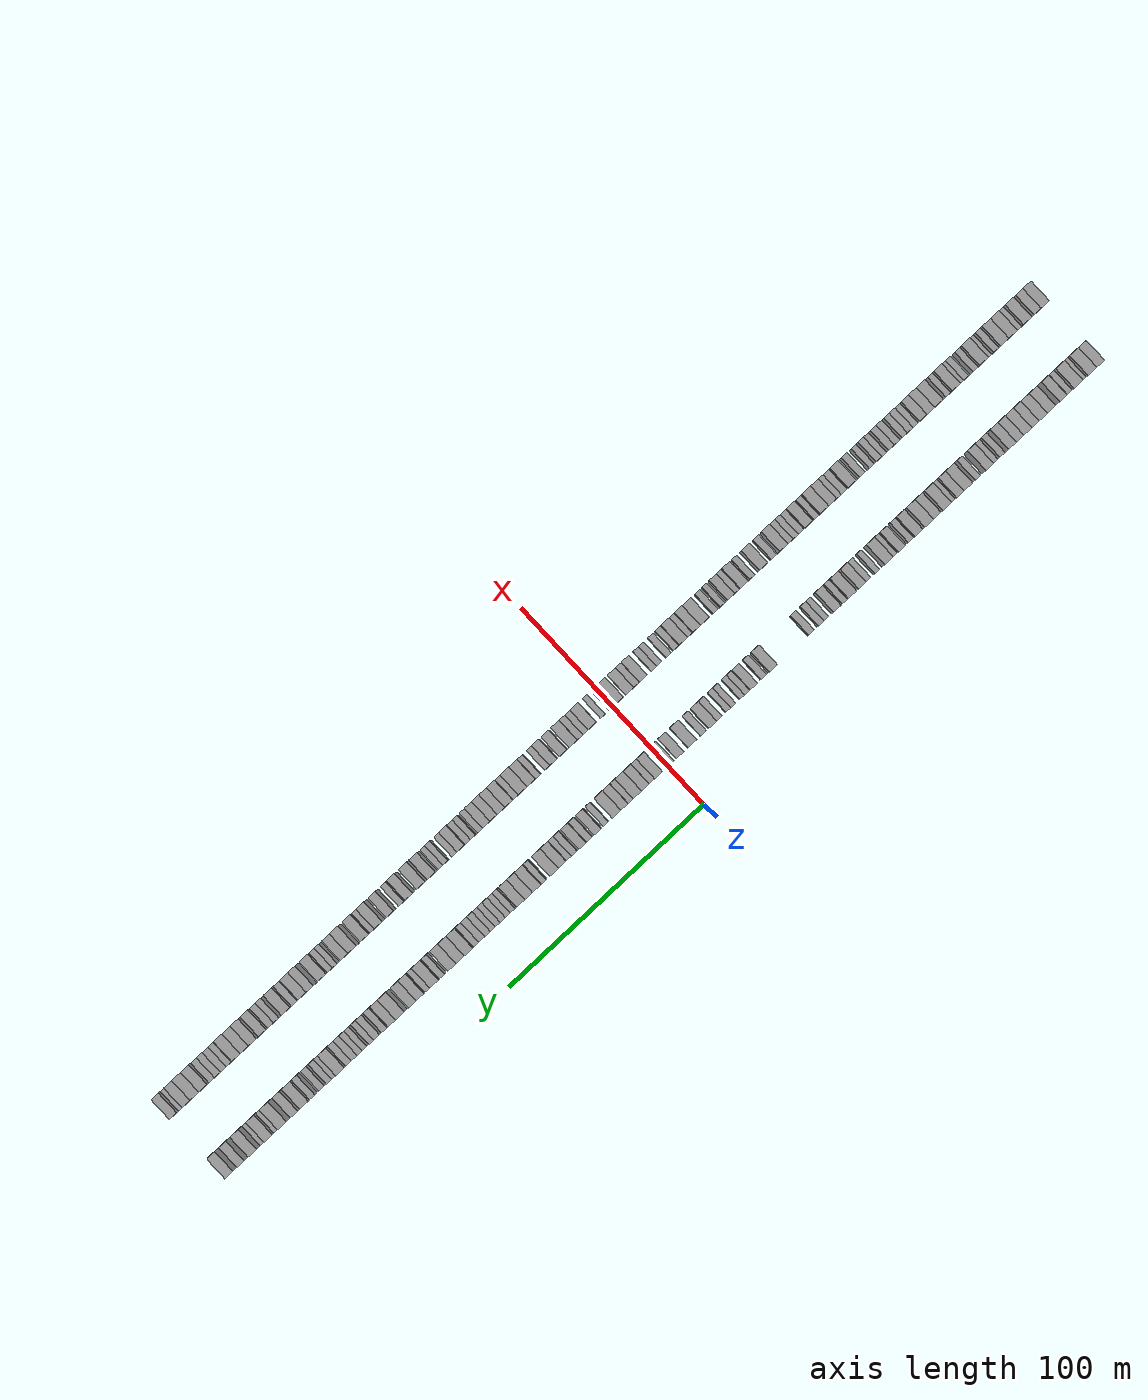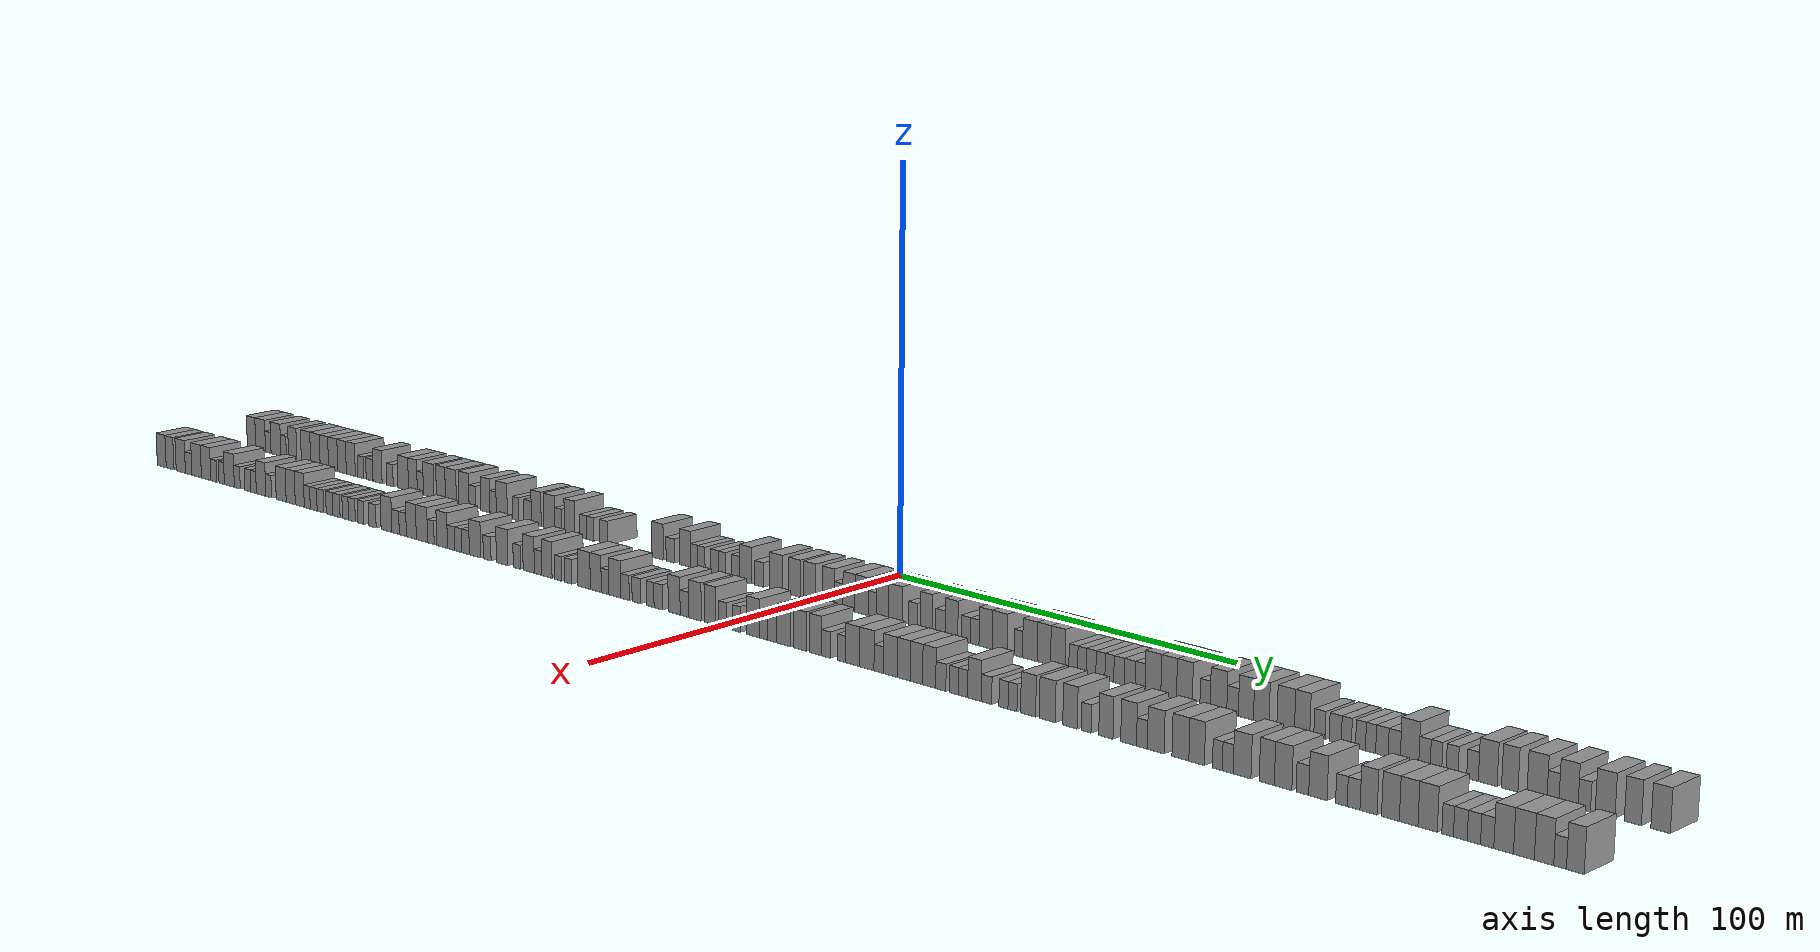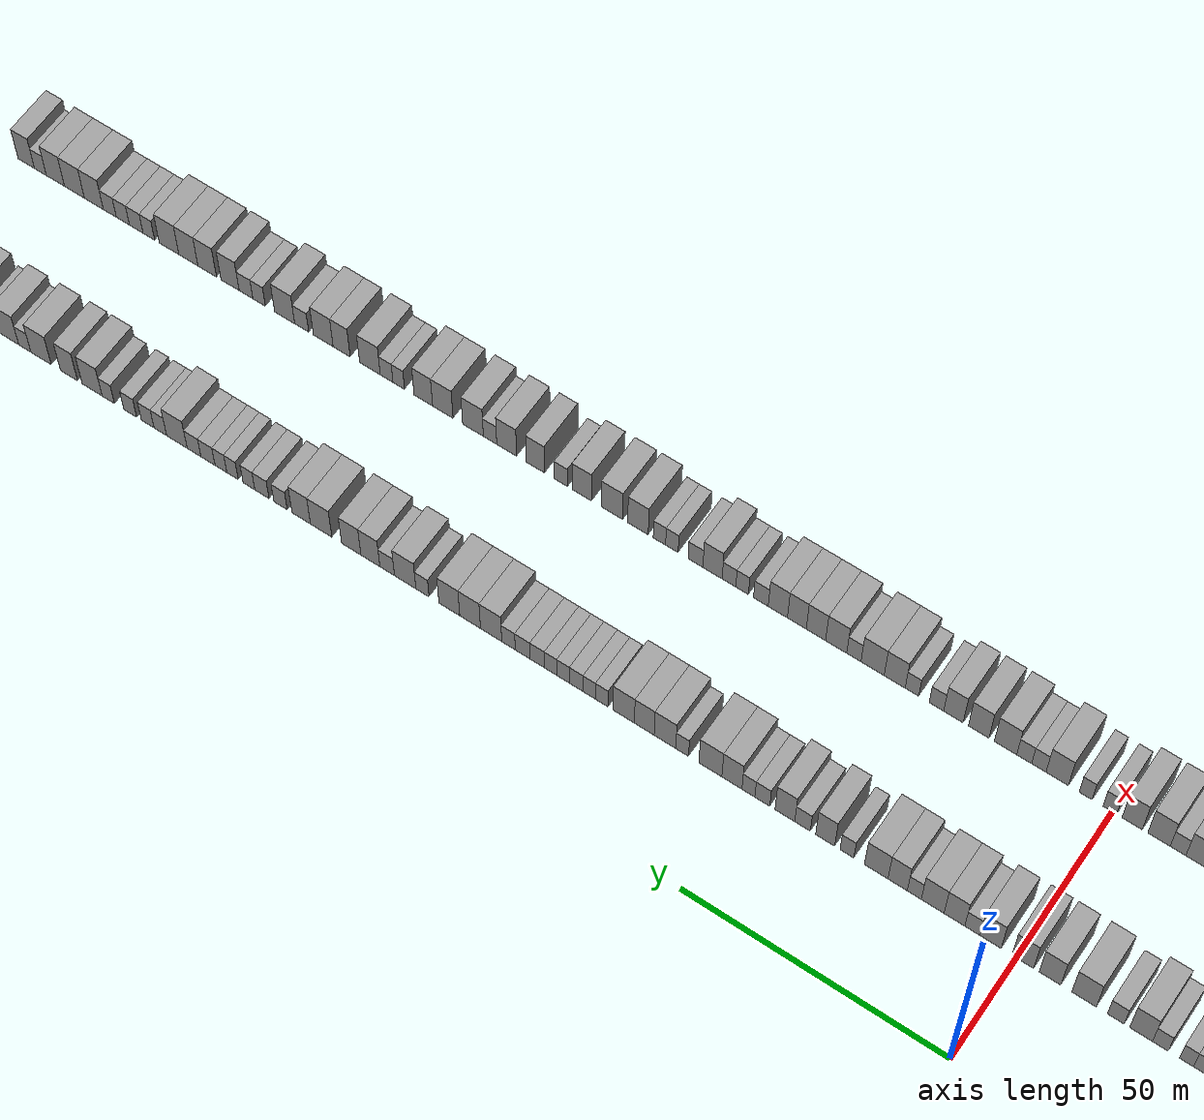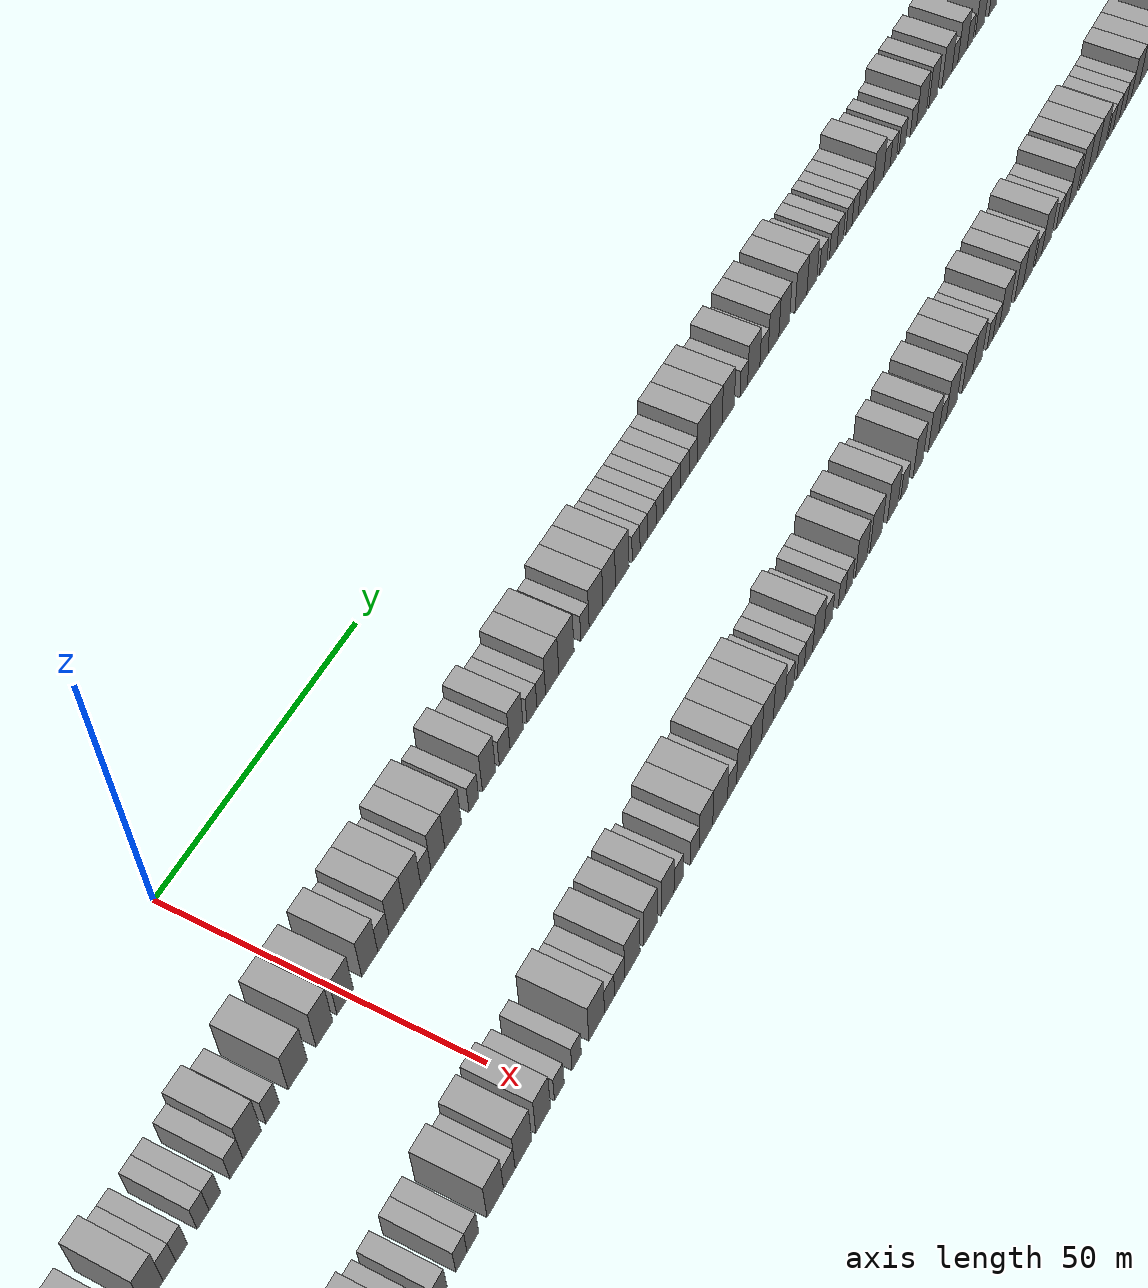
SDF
<sdf version="1.6">
 <world name="default">
  <scene>
   <sky><clouds><speed>12</speed></clouds></sky>
   <ambient>0.4 0.4 0.4 1</ambient>
   <background>0.7 0.7 0.7 1</background>
   <shadows>1</shadows>
  </scene>
  <gravity>0 0 -9.8066</gravity>
  <magnetic_field>6e-06 2.3e-05 -4.2e-05</magnetic_field>
  <physics default="0" name="default_physics" type="ode">
   <ode>
    <solver>
     <type>quick</type>
     <iters>10</iters>
     <sor>1.0</sor>
     <use_dynamic_moi_rescaling>0</use_dynamic_moi_rescaling>
    </solver>
    <constraints>
     <cfm>0</cfm>
     <erp>0.2</erp>
     <contact_max_correcting_vel>100</contact_max_correcting_vel>
     <contact_surface_layer>0.001</contact_surface_layer>
    </constraints>
   </ode>
   <max_step_size>0.004</max_step_size>
   <real_time_factor>1</real_time_factor>
   <real_time_update_rate>250</real_time_update_rate>
  </physics>
  <light name="sun" type="directional">
   <pose>0 0 10 0 0 0</pose>
   <diffuse>0.8 0.8 0.8 1</diffuse>
   <specular>0.2 0.2 0.2 1</specular>
   <attenuation>
    <range>1000</range>
    <constant>0.9</constant>
    <linear>0.01</linear>
    <quadratic>0.001</quadratic>
   </attenuation>
   <direction>-0.5 0.1 -0.9</direction>
  </light>
  <model name="building_1">
   <static>1</static>
   <pose>25.0000 -218.0419 0 0.000000 0.000000 0.000000</pose>
   <link name="link">
    <pose>0 0 4.50 0 0 0</pose>
    <collision name="collision"><geometry><box><size>10.0000 3.9162 9.0000</size></box></geometry></collision>
    <visual name="visual">
     <cast_shadows>0</cast_shadows>
     <geometry><box><size>10.0000 3.9162 9.0000</size></box></geometry>
     <material>
      <script>
       <uri>model://grey_wall/materials/scripts</uri>
       <uri>model://grey_wall/materials/textures</uri>
       <name>vrc/grey_wall</name>
      </script>
     </material>
    </visual>
   </link>
  </model>
  <model name="building_2">
   <static>1</static>
   <pose>25.0000 -213.8533 0 0.000000 0.000000 0.000000</pose>
   <link name="link">
    <pose>0 0 4.50 0 0 0</pose>
    <collision name="collision"><geometry><box><size>10.0000 4.4610 9.0000</size></box></geometry></collision>
    <visual name="visual">
     <cast_shadows>0</cast_shadows>
     <geometry><box><size>10.0000 4.4610 9.0000</size></box></geometry>
     <material>
      <script>
       <uri>model://grey_wall/materials/scripts</uri>
       <uri>model://grey_wall/materials/textures</uri>
       <name>vrc/grey_wall</name>
      </script>
     </material>
    </visual>
   </link>
  </model>
  <model name="building_3">
   <static>1</static>
   <pose>25.0000 -210.3677 0 0.000000 0.000000 0.000000</pose>
   <link name="link">
    <pose>0 0 3.00 0 0 0</pose>
    <collision name="collision"><geometry><box><size>10.0000 2.5101 6.0000</size></box></geometry></collision>
    <visual name="visual">
     <cast_shadows>0</cast_shadows>
     <geometry><box><size>10.0000 2.5101 6.0000</size></box></geometry>
     <material>
      <script>
       <uri>model://grey_wall/materials/scripts</uri>
       <uri>model://grey_wall/materials/textures</uri>
       <name>vrc/grey_wall</name>
      </script>
     </material>
    </visual>
   </link>
  </model>
  <model name="building_4">
   <static>1</static>
   <pose>25.0000 -206.8642 0 0.000000 0.000000 0.000000</pose>
   <link name="link">
    <pose>0 0 4.50 0 0 0</pose>
    <collision name="collision"><geometry><box><size>10.0000 4.4970 9.0000</size></box></geometry></collision>
    <visual name="visual">
     <cast_shadows>0</cast_shadows>
     <geometry><box><size>10.0000 4.4970 9.0000</size></box></geometry>
     <material>
      <script>
       <uri>model://grey_wall/materials/scripts</uri>
       <uri>model://grey_wall/materials/textures</uri>
       <name>vrc/grey_wall</name>
      </script>
     </material>
    </visual>
   </link>
  </model>
  <model name="building_5">
   <static>1</static>
   <pose>25.0000 -203.3650 0 0.000000 0.000000 0.000000</pose>
   <link name="link">
    <pose>0 0 3.00 0 0 0</pose>
    <collision name="collision"><geometry><box><size>10.0000 2.5015 6.0000</size></box></geometry></collision>
    <visual name="visual">
     <cast_shadows>0</cast_shadows>
     <geometry><box><size>10.0000 2.5015 6.0000</size></box></geometry>
     <material>
      <script>
       <uri>model://grey_wall/materials/scripts</uri>
       <uri>model://grey_wall/materials/textures</uri>
       <name>vrc/grey_wall</name>
      </script>
     </material>
    </visual>
   </link>
  </model>
  <model name="building_6">
   <static>1</static>
   <pose>25.0000 -199.2475 0 0.000000 0.000000 0.000000</pose>
   <link name="link">
    <pose>0 0 4.50 0 0 0</pose>
    <collision name="collision"><geometry><box><size>10.0000 3.7333 9.0000</size></box></geometry></collision>
    <visual name="visual">
     <cast_shadows>0</cast_shadows>
     <geometry><box><size>10.0000 3.7333 9.0000</size></box></geometry>
     <material>
      <script>
       <uri>model://grey_wall/materials/scripts</uri>
       <uri>model://grey_wall/materials/textures</uri>
       <name>vrc/grey_wall</name>
      </script>
     </material>
    </visual>
   </link>
  </model>
  <model name="building_7">
   <static>1</static>
   <pose>25.0000 -193.3055 0 0.000000 0.000000 0.000000</pose>
   <link name="link">
    <pose>0 0 4.50 0 0 0</pose>
    <collision name="collision"><geometry><box><size>10.0000 4.1508 9.0000</size></box></geometry></collision>
    <visual name="visual">
     <cast_shadows>0</cast_shadows>
     <geometry><box><size>10.0000 4.1508 9.0000</size></box></geometry>
     <material>
      <script>
       <uri>model://grey_wall/materials/scripts</uri>
       <uri>model://grey_wall/materials/textures</uri>
       <name>vrc/grey_wall</name>
      </script>
     </material>
    </visual>
   </link>
  </model>
  <model name="building_8">
   <static>1</static>
   <pose>25.0000 -189.1234 0 0.000000 0.000000 0.000000</pose>
   <link name="link">
    <pose>0 0 4.50 0 0 0</pose>
    <collision name="collision"><geometry><box><size>10.0000 4.2133 9.0000</size></box></geometry></collision>
    <visual name="visual">
     <cast_shadows>0</cast_shadows>
     <geometry><box><size>10.0000 4.2133 9.0000</size></box></geometry>
     <material>
      <script>
       <uri>model://grey_wall/materials/scripts</uri>
       <uri>model://grey_wall/materials/textures</uri>
       <name>vrc/grey_wall</name>
      </script>
     </material>
    </visual>
   </link>
  </model>
  <model name="building_9">
   <static>1</static>
   <pose>25.0000 -185.1619 0 0.000000 0.000000 0.000000</pose>
   <link name="link">
    <pose>0 0 4.50 0 0 0</pose>
    <collision name="collision"><geometry><box><size>10.0000 3.7097 9.0000</size></box></geometry></collision>
    <visual name="visual">
     <cast_shadows>0</cast_shadows>
     <geometry><box><size>10.0000 3.7097 9.0000</size></box></geometry>
     <material>
      <script>
       <uri>model://grey_wall/materials/scripts</uri>
       <uri>model://grey_wall/materials/textures</uri>
       <name>vrc/grey_wall</name>
      </script>
     </material>
    </visual>
   </link>
  </model>
  <model name="building_10">
   <static>1</static>
   <pose>25.0000 -181.2895 0 0.000000 0.000000 0.000000</pose>
   <link name="link">
    <pose>0 0 4.50 0 0 0</pose>
    <collision name="collision"><geometry><box><size>10.0000 4.0353 9.0000</size></box></geometry></collision>
    <visual name="visual">
     <cast_shadows>0</cast_shadows>
     <geometry><box><size>10.0000 4.0353 9.0000</size></box></geometry>
     <material>
      <script>
       <uri>model://grey_wall/materials/scripts</uri>
       <uri>model://grey_wall/materials/textures</uri>
       <name>vrc/grey_wall</name>
      </script>
     </material>
    </visual>
   </link>
  </model>
  <model name="building_11">
   <static>1</static>
   <pose>25.0000 -177.4134 0 0.000000 0.000000 0.000000</pose>
   <link name="link">
    <pose>0 0 4.50 0 0 0</pose>
    <collision name="collision"><geometry><box><size>10.0000 3.7169 9.0000</size></box></geometry></collision>
    <visual name="visual">
     <cast_shadows>0</cast_shadows>
     <geometry><box><size>10.0000 3.7169 9.0000</size></box></geometry>
     <material>
      <script>
       <uri>model://grey_wall/materials/scripts</uri>
       <uri>model://grey_wall/materials/textures</uri>
       <name>vrc/grey_wall</name>
      </script>
     </material>
    </visual>
   </link>
  </model>
  <model name="building_12">
   <static>1</static>
   <pose>25.0000 -173.5916 0 0.000000 0.000000 0.000000</pose>
   <link name="link">
    <pose>0 0 4.50 0 0 0</pose>
    <collision name="collision"><geometry><box><size>10.0000 3.9268 9.0000</size></box></geometry></collision>
    <visual name="visual">
     <cast_shadows>0</cast_shadows>
     <geometry><box><size>10.0000 3.9268 9.0000</size></box></geometry>
     <material>
      <script>
       <uri>model://grey_wall/materials/scripts</uri>
       <uri>model://grey_wall/materials/textures</uri>
       <name>vrc/grey_wall</name>
      </script>
     </material>
    </visual>
   </link>
  </model>
  <model name="building_13">
   <static>1</static>
   <pose>25.0000 -169.3011 0 0.000000 0.000000 0.000000</pose>
   <link name="link">
    <pose>0 0 3.00 0 0 0</pose>
    <collision name="collision"><geometry><box><size>10.0000 2.6542 6.0000</size></box></geometry></collision>
    <visual name="visual">
     <cast_shadows>0</cast_shadows>
     <geometry><box><size>10.0000 2.6542 6.0000</size></box></geometry>
     <material>
      <script>
       <uri>model://grey_wall/materials/scripts</uri>
       <uri>model://grey_wall/materials/textures</uri>
       <name>vrc/grey_wall</name>
      </script>
     </material>
    </visual>
   </link>
  </model>
  <model name="building_14">
   <static>1</static>
   <pose>25.0000 -165.5096 0 0.000000 0.000000 0.000000</pose>
   <link name="link">
    <pose>0 0 3.00 0 0 0</pose>
    <collision name="collision"><geometry><box><size>10.0000 2.9288 6.0000</size></box></geometry></collision>
    <visual name="visual">
     <cast_shadows>0</cast_shadows>
     <geometry><box><size>10.0000 2.9288 6.0000</size></box></geometry>
     <material>
      <script>
       <uri>model://grey_wall/materials/scripts</uri>
       <uri>model://grey_wall/materials/textures</uri>
       <name>vrc/grey_wall</name>
      </script>
     </material>
    </visual>
   </link>
  </model>
  <model name="building_15">
   <static>1</static>
   <pose>25.0000 -162.1145 0 0.000000 0.000000 0.000000</pose>
   <link name="link">
    <pose>0 0 4.50 0 0 0</pose>
    <collision name="collision"><geometry><box><size>10.0000 3.8613 9.0000</size></box></geometry></collision>
    <visual name="visual">
     <cast_shadows>0</cast_shadows>
     <geometry><box><size>10.0000 3.8613 9.0000</size></box></geometry>
     <material>
      <script>
       <uri>model://grey_wall/materials/scripts</uri>
       <uri>model://grey_wall/materials/textures</uri>
       <name>vrc/grey_wall</name>
      </script>
     </material>
    </visual>
   </link>
  </model>
  <model name="building_16">
   <static>1</static>
   <pose>25.0000 -156.8311 0 0.000000 0.000000 0.000000</pose>
   <link name="link">
    <pose>0 0 3.00 0 0 0</pose>
    <collision name="collision"><geometry><box><size>10.0000 2.7055 6.0000</size></box></geometry></collision>
    <visual name="visual">
     <cast_shadows>0</cast_shadows>
     <geometry><box><size>10.0000 2.7055 6.0000</size></box></geometry>
     <material>
      <script>
       <uri>model://grey_wall/materials/scripts</uri>
       <uri>model://grey_wall/materials/textures</uri>
       <name>vrc/grey_wall</name>
      </script>
     </material>
    </visual>
   </link>
  </model>
  <model name="building_17">
   <static>1</static>
   <pose>25.0000 -151.2708 0 0.000000 0.000000 0.000000</pose>
   <link name="link">
    <pose>0 0 4.50 0 0 0</pose>
    <collision name="collision"><geometry><box><size>10.0000 4.4152 9.0000</size></box></geometry></collision>
    <visual name="visual">
     <cast_shadows>0</cast_shadows>
     <geometry><box><size>10.0000 4.4152 9.0000</size></box></geometry>
     <material>
      <script>
       <uri>model://grey_wall/materials/scripts</uri>
       <uri>model://grey_wall/materials/textures</uri>
       <name>vrc/grey_wall</name>
      </script>
     </material>
    </visual>
   </link>
  </model>
  <model name="building_18">
   <static>1</static>
   <pose>25.0000 -147.2323 0 0.000000 0.000000 0.000000</pose>
   <link name="link">
    <pose>0 0 4.50 0 0 0</pose>
    <collision name="collision"><geometry><box><size>10.0000 3.6618 9.0000</size></box></geometry></collision>
    <visual name="visual">
     <cast_shadows>0</cast_shadows>
     <geometry><box><size>10.0000 3.6618 9.0000</size></box></geometry>
     <material>
      <script>
       <uri>model://grey_wall/materials/scripts</uri>
       <uri>model://grey_wall/materials/textures</uri>
       <name>vrc/grey_wall</name>
      </script>
     </material>
    </visual>
   </link>
  </model>
  <model name="building_19">
   <static>1</static>
   <pose>25.0000 -144.1342 0 0.000000 0.000000 0.000000</pose>
   <link name="link">
    <pose>0 0 3.00 0 0 0</pose>
    <collision name="collision"><geometry><box><size>10.0000 2.5345 6.0000</size></box></geometry></collision>
    <visual name="visual">
     <cast_shadows>0</cast_shadows>
     <geometry><box><size>10.0000 2.5345 6.0000</size></box></geometry>
     <material>
      <script>
       <uri>model://grey_wall/materials/scripts</uri>
       <uri>model://grey_wall/materials/textures</uri>
       <name>vrc/grey_wall</name>
      </script>
     </material>
    </visual>
   </link>
  </model>
  <model name="building_20">
   <static>1</static>
   <pose>25.0000 -140.6970 0 0.000000 0.000000 0.000000</pose>
   <link name="link">
    <pose>0 0 4.50 0 0 0</pose>
    <collision name="collision"><geometry><box><size>10.0000 4.3400 9.0000</size></box></geometry></collision>
    <visual name="visual">
     <cast_shadows>0</cast_shadows>
     <geometry><box><size>10.0000 4.3400 9.0000</size></box></geometry>
     <material>
      <script>
       <uri>model://grey_wall/materials/scripts</uri>
       <uri>model://grey_wall/materials/textures</uri>
       <name>vrc/grey_wall</name>
      </script>
     </material>
    </visual>
   </link>
  </model>
  <model name="building_21">
   <static>1</static>
   <pose>25.0000 -135.6771 0 0.000000 0.000000 0.000000</pose>
   <link name="link">
    <pose>0 0 4.50 0 0 0</pose>
    <collision name="collision"><geometry><box><size>10.0000 3.6997 9.0000</size></box></geometry></collision>
    <visual name="visual">
     <cast_shadows>0</cast_shadows>
     <geometry><box><size>10.0000 3.6997 9.0000</size></box></geometry>
     <material>
      <script>
       <uri>model://grey_wall/materials/scripts</uri>
       <uri>model://grey_wall/materials/textures</uri>
       <name>vrc/grey_wall</name>
      </script>
     </material>
    </visual>
   </link>
  </model>
  <model name="building_22">
   <static>1</static>
   <pose>25.0000 -131.6127 0 0.000000 0.000000 0.000000</pose>
   <link name="link">
    <pose>0 0 4.50 0 0 0</pose>
    <collision name="collision"><geometry><box><size>10.0000 4.4293 9.0000</size></box></geometry></collision>
    <visual name="visual">
     <cast_shadows>0</cast_shadows>
     <geometry><box><size>10.0000 4.4293 9.0000</size></box></geometry>
     <material>
      <script>
       <uri>model://grey_wall/materials/scripts</uri>
       <uri>model://grey_wall/materials/textures</uri>
       <name>vrc/grey_wall</name>
      </script>
     </material>
    </visual>
   </link>
  </model>
  <model name="building_23">
   <static>1</static>
   <pose>25.0000 -126.3371 0 0.000000 0.000000 0.000000</pose>
   <link name="link">
    <pose>0 0 4.50 0 0 0</pose>
    <collision name="collision"><geometry><box><size>10.0000 4.1219 9.0000</size></box></geometry></collision>
    <visual name="visual">
     <cast_shadows>0</cast_shadows>
     <geometry><box><size>10.0000 4.1219 9.0000</size></box></geometry>
     <material>
      <script>
       <uri>model://grey_wall/materials/scripts</uri>
       <uri>model://grey_wall/materials/textures</uri>
       <name>vrc/grey_wall</name>
      </script>
     </material>
    </visual>
   </link>
  </model>
  <model name="building_24">
   <static>1</static>
   <pose>25.0000 -122.9397 0 0.000000 0.000000 0.000000</pose>
   <link name="link">
    <pose>0 0 3.00 0 0 0</pose>
    <collision name="collision"><geometry><box><size>10.0000 2.6730 6.0000</size></box></geometry></collision>
    <visual name="visual">
     <cast_shadows>0</cast_shadows>
     <geometry><box><size>10.0000 2.6730 6.0000</size></box></geometry>
     <material>
      <script>
       <uri>model://grey_wall/materials/scripts</uri>
       <uri>model://grey_wall/materials/textures</uri>
       <name>vrc/grey_wall</name>
      </script>
     </material>
    </visual>
   </link>
  </model>
  <model name="building_25">
   <static>1</static>
   <pose>25.0000 -117.7783 0 0.000000 0.000000 0.000000</pose>
   <link name="link">
    <pose>0 0 4.50 0 0 0</pose>
    <collision name="collision"><geometry><box><size>10.0000 3.6497 9.0000</size></box></geometry></collision>
    <visual name="visual">
     <cast_shadows>0</cast_shadows>
     <geometry><box><size>10.0000 3.6497 9.0000</size></box></geometry>
     <material>
      <script>
       <uri>model://grey_wall/materials/scripts</uri>
       <uri>model://grey_wall/materials/textures</uri>
       <name>vrc/grey_wall</name>
      </script>
     </material>
    </visual>
   </link>
  </model>
  <model name="building_26">
   <static>1</static>
   <pose>25.0000 -114.7021 0 0.000000 0.000000 0.000000</pose>
   <link name="link">
    <pose>0 0 3.00 0 0 0</pose>
    <collision name="collision"><geometry><box><size>10.0000 2.5026 6.0000</size></box></geometry></collision>
    <visual name="visual">
     <cast_shadows>0</cast_shadows>
     <geometry><box><size>10.0000 2.5026 6.0000</size></box></geometry>
     <material>
      <script>
       <uri>model://grey_wall/materials/scripts</uri>
       <uri>model://grey_wall/materials/textures</uri>
       <name>vrc/grey_wall</name>
      </script>
     </material>
    </visual>
   </link>
  </model>
  <model name="building_27">
   <static>1</static>
   <pose>25.0000 -111.2873 0 0.000000 0.000000 0.000000</pose>
   <link name="link">
    <pose>0 0 4.50 0 0 0</pose>
    <collision name="collision"><geometry><box><size>10.0000 4.3269 9.0000</size></box></geometry></collision>
    <visual name="visual">
     <cast_shadows>0</cast_shadows>
     <geometry><box><size>10.0000 4.3269 9.0000</size></box></geometry>
     <material>
      <script>
       <uri>model://grey_wall/materials/scripts</uri>
       <uri>model://grey_wall/materials/textures</uri>
       <name>vrc/grey_wall</name>
      </script>
     </material>
    </visual>
   </link>
  </model>
  <model name="building_28">
   <static>1</static>
   <pose>25.0000 -105.9201 0 0.000000 0.000000 0.000000</pose>
   <link name="link">
    <pose>0 0 3.00 0 0 0</pose>
    <collision name="collision"><geometry><box><size>10.0000 2.4074 6.0000</size></box></geometry></collision>
    <visual name="visual">
     <cast_shadows>0</cast_shadows>
     <geometry><box><size>10.0000 2.4074 6.0000</size></box></geometry>
     <material>
      <script>
       <uri>model://grey_wall/materials/scripts</uri>
       <uri>model://grey_wall/materials/textures</uri>
       <name>vrc/grey_wall</name>
      </script>
     </material>
    </visual>
   </link>
  </model>
  <model name="building_29">
   <static>1</static>
   <pose>25.0000 -101.2425 0 0.000000 0.000000 0.000000</pose>
   <link name="link">
    <pose>0 0 3.00 0 0 0</pose>
    <collision name="collision"><geometry><box><size>10.0000 2.9478 6.0000</size></box></geometry></collision>
    <visual name="visual">
     <cast_shadows>0</cast_shadows>
     <geometry><box><size>10.0000 2.9478 6.0000</size></box></geometry>
     <material>
      <script>
       <uri>model://grey_wall/materials/scripts</uri>
       <uri>model://grey_wall/materials/textures</uri>
       <name>vrc/grey_wall</name>
      </script>
     </material>
    </visual>
   </link>
  </model>
  <model name="building_30">
   <static>1</static>
   <pose>25.0000 -97.8844 0 0.000000 0.000000 0.000000</pose>
   <link name="link">
    <pose>0 0 4.50 0 0 0</pose>
    <collision name="collision"><geometry><box><size>10.0000 3.7685 9.0000</size></box></geometry></collision>
    <visual name="visual">
     <cast_shadows>0</cast_shadows>
     <geometry><box><size>10.0000 3.7685 9.0000</size></box></geometry>
     <material>
      <script>
       <uri>model://grey_wall/materials/scripts</uri>
       <uri>model://grey_wall/materials/textures</uri>
       <name>vrc/grey_wall</name>
      </script>
     </material>
    </visual>
   </link>
  </model>
  <model name="building_31">
   <static>1</static>
   <pose>25.0000 -92.9036 0 0.000000 0.000000 0.000000</pose>
   <link name="link">
    <pose>0 0 4.50 0 0 0</pose>
    <collision name="collision"><geometry><box><size>10.0000 4.1931 9.0000</size></box></geometry></collision>
    <visual name="visual">
     <cast_shadows>0</cast_shadows>
     <geometry><box><size>10.0000 4.1931 9.0000</size></box></geometry>
     <material>
      <script>
       <uri>model://grey_wall/materials/scripts</uri>
       <uri>model://grey_wall/materials/textures</uri>
       <name>vrc/grey_wall</name>
      </script>
     </material>
    </visual>
   </link>
  </model>
  <model name="building_32">
   <static>1</static>
   <pose>25.0000 -89.4860 0 0.000000 0.000000 0.000000</pose>
   <link name="link">
    <pose>0 0 3.00 0 0 0</pose>
    <collision name="collision"><geometry><box><size>10.0000 2.6422 6.0000</size></box></geometry></collision>
    <visual name="visual">
     <cast_shadows>0</cast_shadows>
     <geometry><box><size>10.0000 2.6422 6.0000</size></box></geometry>
     <material>
      <script>
       <uri>model://grey_wall/materials/scripts</uri>
       <uri>model://grey_wall/materials/textures</uri>
       <name>vrc/grey_wall</name>
      </script>
     </material>
    </visual>
   </link>
  </model>
  <model name="building_33">
   <static>1</static>
   <pose>25.0000 -85.2763 0 0.000000 0.000000 0.000000</pose>
   <link name="link">
    <pose>0 0 4.50 0 0 0</pose>
    <collision name="collision"><geometry><box><size>10.0000 3.7771 9.0000</size></box></geometry></collision>
    <visual name="visual">
     <cast_shadows>0</cast_shadows>
     <geometry><box><size>10.0000 3.7771 9.0000</size></box></geometry>
     <material>
      <script>
       <uri>model://grey_wall/materials/scripts</uri>
       <uri>model://grey_wall/materials/textures</uri>
       <name>vrc/grey_wall</name>
      </script>
     </material>
    </visual>
   </link>
  </model>
  <model name="building_34">
   <static>1</static>
   <pose>25.0000 -80.1502 0 0.000000 0.000000 0.000000</pose>
   <link name="link">
    <pose>0 0 3.00 0 0 0</pose>
    <collision name="collision"><geometry><box><size>10.0000 2.4752 6.0000</size></box></geometry></collision>
    <visual name="visual">
     <cast_shadows>0</cast_shadows>
     <geometry><box><size>10.0000 2.4752 6.0000</size></box></geometry>
     <material>
      <script>
       <uri>model://grey_wall/materials/scripts</uri>
       <uri>model://grey_wall/materials/textures</uri>
       <name>vrc/grey_wall</name>
      </script>
     </material>
    </visual>
   </link>
  </model>
  <model name="building_35">
   <static>1</static>
   <pose>25.0000 -77.5133 0 0.000000 0.000000 0.000000</pose>
   <link name="link">
    <pose>0 0 3.00 0 0 0</pose>
    <collision name="collision"><geometry><box><size>10.0000 2.7986 6.0000</size></box></geometry></collision>
    <visual name="visual">
     <cast_shadows>0</cast_shadows>
     <geometry><box><size>10.0000 2.7986 6.0000</size></box></geometry>
     <material>
      <script>
       <uri>model://grey_wall/materials/scripts</uri>
       <uri>model://grey_wall/materials/textures</uri>
       <name>vrc/grey_wall</name>
      </script>
     </material>
    </visual>
   </link>
  </model>
  <model name="building_36">
   <static>1</static>
   <pose>25.0000 -72.6482 0 0.000000 0.000000 0.000000</pose>
   <link name="link">
    <pose>0 0 3.00 0 0 0</pose>
    <collision name="collision"><geometry><box><size>10.0000 2.9316 6.0000</size></box></geometry></collision>
    <visual name="visual">
     <cast_shadows>0</cast_shadows>
     <geometry><box><size>10.0000 2.9316 6.0000</size></box></geometry>
     <material>
      <script>
       <uri>model://grey_wall/materials/scripts</uri>
       <uri>model://grey_wall/materials/textures</uri>
       <name>vrc/grey_wall</name>
      </script>
     </material>
    </visual>
   </link>
  </model>
  <model name="building_37">
   <static>1</static>
   <pose>25.0000 -53.0157 0 0.000000 0.000000 0.000000</pose>
   <link name="link">
    <pose>0 0 4.50 0 0 0</pose>
    <collision name="collision"><geometry><box><size>10.0000 4.1112 9.0000</size></box></geometry></collision>
    <visual name="visual">
     <cast_shadows>0</cast_shadows>
     <geometry><box><size>10.0000 4.1112 9.0000</size></box></geometry>
     <material>
      <script>
       <uri>model://grey_wall/materials/scripts</uri>
       <uri>model://grey_wall/materials/textures</uri>
       <name>vrc/grey_wall</name>
      </script>
     </material>
    </visual>
   </link>
  </model>
  <model name="building_38">
   <static>1</static>
   <pose>25.0000 -48.5144 0 0.000000 0.000000 0.000000</pose>
   <link name="link">
    <pose>0 0 3.00 0 0 0</pose>
    <collision name="collision"><geometry><box><size>10.0000 2.8913 6.0000</size></box></geometry></collision>
    <visual name="visual">
     <cast_shadows>0</cast_shadows>
     <geometry><box><size>10.0000 2.8913 6.0000</size></box></geometry>
     <material>
      <script>
       <uri>model://grey_wall/materials/scripts</uri>
       <uri>model://grey_wall/materials/textures</uri>
       <name>vrc/grey_wall</name>
      </script>
     </material>
    </visual>
   </link>
  </model>
  <model name="building_39">
   <static>1</static>
   <pose>25.0000 -43.2031 0 0.000000 0.000000 0.000000</pose>
   <link name="link">
    <pose>0 0 4.50 0 0 0</pose>
    <collision name="collision"><geometry><box><size>10.0000 3.7314 9.0000</size></box></geometry></collision>
    <visual name="visual">
     <cast_shadows>0</cast_shadows>
     <geometry><box><size>10.0000 3.7314 9.0000</size></box></geometry>
     <material>
      <script>
       <uri>model://grey_wall/materials/scripts</uri>
       <uri>model://grey_wall/materials/textures</uri>
       <name>vrc/grey_wall</name>
      </script>
     </material>
    </visual>
   </link>
  </model>
  <model name="building_40">
   <static>1</static>
   <pose>25.0000 -40.0389 0 0.000000 0.000000 0.000000</pose>
   <link name="link">
    <pose>0 0 3.00 0 0 0</pose>
    <collision name="collision"><geometry><box><size>10.0000 2.5972 6.0000</size></box></geometry></collision>
    <visual name="visual">
     <cast_shadows>0</cast_shadows>
     <geometry><box><size>10.0000 2.5972 6.0000</size></box></geometry>
     <material>
      <script>
       <uri>model://grey_wall/materials/scripts</uri>
       <uri>model://grey_wall/materials/textures</uri>
       <name>vrc/grey_wall</name>
      </script>
     </material>
    </visual>
   </link>
  </model>
  <model name="building_41">
   <static>1</static>
   <pose>25.0000 -37.5212 0 0.000000 0.000000 0.000000</pose>
   <link name="link">
    <pose>0 0 3.00 0 0 0</pose>
    <collision name="collision"><geometry><box><size>10.0000 2.4381 6.0000</size></box></geometry></collision>
    <visual name="visual">
     <cast_shadows>0</cast_shadows>
     <geometry><box><size>10.0000 2.4381 6.0000</size></box></geometry>
     <material>
      <script>
       <uri>model://grey_wall/materials/scripts</uri>
       <uri>model://grey_wall/materials/textures</uri>
       <name>vrc/grey_wall</name>
      </script>
     </material>
    </visual>
   </link>
  </model>
  <model name="building_42">
   <static>1</static>
   <pose>25.0000 -33.0255 0 0.000000 0.000000 0.000000</pose>
   <link name="link">
    <pose>0 0 3.00 0 0 0</pose>
    <collision name="collision"><geometry><box><size>10.0000 2.5532 6.0000</size></box></geometry></collision>
    <visual name="visual">
     <cast_shadows>0</cast_shadows>
     <geometry><box><size>10.0000 2.5532 6.0000</size></box></geometry>
     <material>
      <script>
       <uri>model://grey_wall/materials/scripts</uri>
       <uri>model://grey_wall/materials/textures</uri>
       <name>vrc/grey_wall</name>
      </script>
     </material>
    </visual>
   </link>
  </model>
  <model name="building_43">
   <static>1</static>
   <pose>25.0000 -30.5121 0 0.000000 0.000000 0.000000</pose>
   <link name="link">
    <pose>0 0 3.00 0 0 0</pose>
    <collision name="collision"><geometry><box><size>10.0000 2.4736 6.0000</size></box></geometry></collision>
    <visual name="visual">
     <cast_shadows>0</cast_shadows>
     <geometry><box><size>10.0000 2.4736 6.0000</size></box></geometry>
     <material>
      <script>
       <uri>model://grey_wall/materials/scripts</uri>
       <uri>model://grey_wall/materials/textures</uri>
       <name>vrc/grey_wall</name>
      </script>
     </material>
    </visual>
   </link>
  </model>
  <model name="building_44">
   <static>1</static>
   <pose>25.0000 -25.8657 0 0.000000 0.000000 0.000000</pose>
   <link name="link">
    <pose>0 0 3.00 0 0 0</pose>
    <collision name="collision"><geometry><box><size>10.0000 2.8192 6.0000</size></box></geometry></collision>
    <visual name="visual">
     <cast_shadows>0</cast_shadows>
     <geometry><box><size>10.0000 2.8192 6.0000</size></box></geometry>
     <material>
      <script>
       <uri>model://grey_wall/materials/scripts</uri>
       <uri>model://grey_wall/materials/textures</uri>
       <name>vrc/grey_wall</name>
      </script>
     </material>
    </visual>
   </link>
  </model>
  <model name="building_45">
   <static>1</static>
   <pose>25.0000 -22.4198 0 0.000000 0.000000 0.000000</pose>
   <link name="link">
    <pose>0 0 4.50 0 0 0</pose>
    <collision name="collision"><geometry><box><size>10.0000 4.0725 9.0000</size></box></geometry></collision>
    <visual name="visual">
     <cast_shadows>0</cast_shadows>
     <geometry><box><size>10.0000 4.0725 9.0000</size></box></geometry>
     <material>
      <script>
       <uri>model://grey_wall/materials/scripts</uri>
       <uri>model://grey_wall/materials/textures</uri>
       <name>vrc/grey_wall</name>
      </script>
     </material>
    </visual>
   </link>
  </model>
  <model name="building_46">
   <static>1</static>
   <pose>25.0000 -17.8843 0 0.000000 0.000000 0.000000</pose>
   <link name="link">
    <pose>0 0 3.00 0 0 0</pose>
    <collision name="collision"><geometry><box><size>10.0000 2.9986 6.0000</size></box></geometry></collision>
    <visual name="visual">
     <cast_shadows>0</cast_shadows>
     <geometry><box><size>10.0000 2.9986 6.0000</size></box></geometry>
     <material>
      <script>
       <uri>model://grey_wall/materials/scripts</uri>
       <uri>model://grey_wall/materials/textures</uri>
       <name>vrc/grey_wall</name>
      </script>
     </material>
    </visual>
   </link>
  </model>
  <model name="building_47">
   <static>1</static>
   <pose>25.0000 -12.1722 0 0.000000 0.000000 0.000000</pose>
   <link name="link">
    <pose>0 0 4.50 0 0 0</pose>
    <collision name="collision"><geometry><box><size>10.0000 4.4255 9.0000</size></box></geometry></collision>
    <visual name="visual">
     <cast_shadows>0</cast_shadows>
     <geometry><box><size>10.0000 4.4255 9.0000</size></box></geometry>
     <material>
      <script>
       <uri>model://grey_wall/materials/scripts</uri>
       <uri>model://grey_wall/materials/textures</uri>
       <name>vrc/grey_wall</name>
      </script>
     </material>
    </visual>
   </link>
  </model>
  <model name="building_48">
   <static>1</static>
   <pose>25.0000 -5.9985 0 0.000000 0.000000 0.000000</pose>
   <link name="link">
    <pose>0 0 4.50 0 0 0</pose>
    <collision name="collision"><geometry><box><size>10.0000 3.9220 9.0000</size></box></geometry></collision>
    <visual name="visual">
     <cast_shadows>0</cast_shadows>
     <geometry><box><size>10.0000 3.9220 9.0000</size></box></geometry>
     <material>
      <script>
       <uri>model://grey_wall/materials/scripts</uri>
       <uri>model://grey_wall/materials/textures</uri>
       <name>vrc/grey_wall</name>
      </script>
     </material>
    </visual>
   </link>
  </model>
  <model name="building_49">
   <static>1</static>
   <pose>25.0000 -1.0653 0 0.000000 0.000000 0.000000</pose>
   <link name="link">
    <pose>0 0 4.50 0 0 0</pose>
    <collision name="collision"><geometry><box><size>10.0000 3.9443 9.0000</size></box></geometry></collision>
    <visual name="visual">
     <cast_shadows>0</cast_shadows>
     <geometry><box><size>10.0000 3.9443 9.0000</size></box></geometry>
     <material>
      <script>
       <uri>model://grey_wall/materials/scripts</uri>
       <uri>model://grey_wall/materials/textures</uri>
       <name>vrc/grey_wall</name>
      </script>
     </material>
    </visual>
   </link>
  </model>
  <model name="building_50">
   <static>1</static>
   <pose>25.0000 4.8676 0 0.000000 0.000000 0.000000</pose>
   <link name="link">
    <pose>0 0 4.50 0 0 0</pose>
    <collision name="collision"><geometry><box><size>10.0000 3.9215 9.0000</size></box></geometry></collision>
    <visual name="visual">
     <cast_shadows>0</cast_shadows>
     <geometry><box><size>10.0000 3.9215 9.0000</size></box></geometry>
     <material>
      <script>
       <uri>model://grey_wall/materials/scripts</uri>
       <uri>model://grey_wall/materials/textures</uri>
       <name>vrc/grey_wall</name>
      </script>
     </material>
    </visual>
   </link>
  </model>
  <model name="building_51">
   <static>1</static>
   <pose>25.0000 8.2137 0 0.000000 0.000000 0.000000</pose>
   <link name="link">
    <pose>0 0 3.00 0 0 0</pose>
    <collision name="collision"><geometry><box><size>10.0000 2.7707 6.0000</size></box></geometry></collision>
    <visual name="visual">
     <cast_shadows>0</cast_shadows>
     <geometry><box><size>10.0000 2.7707 6.0000</size></box></geometry>
     <material>
      <script>
       <uri>model://grey_wall/materials/scripts</uri>
       <uri>model://grey_wall/materials/textures</uri>
       <name>vrc/grey_wall</name>
      </script>
     </material>
    </visual>
   </link>
  </model>
  <model name="building_52">
   <static>1</static>
   <pose>25.0000 11.5132 0 0.000000 0.000000 0.000000</pose>
   <link name="link">
    <pose>0 0 4.50 0 0 0</pose>
    <collision name="collision"><geometry><box><size>10.0000 3.8282 9.0000</size></box></geometry></collision>
    <visual name="visual">
     <cast_shadows>0</cast_shadows>
     <geometry><box><size>10.0000 3.8282 9.0000</size></box></geometry>
     <material>
      <script>
       <uri>model://grey_wall/materials/scripts</uri>
       <uri>model://grey_wall/materials/textures</uri>
       <name>vrc/grey_wall</name>
      </script>
     </material>
    </visual>
   </link>
  </model>
  <model name="building_53">
   <static>1</static>
   <pose>25.0000 15.5393 0 0.000000 0.000000 0.000000</pose>
   <link name="link">
    <pose>0 0 4.50 0 0 0</pose>
    <collision name="collision"><geometry><box><size>10.0000 4.2240 9.0000</size></box></geometry></collision>
    <visual name="visual">
     <cast_shadows>0</cast_shadows>
     <geometry><box><size>10.0000 4.2240 9.0000</size></box></geometry>
     <material>
      <script>
       <uri>model://grey_wall/materials/scripts</uri>
       <uri>model://grey_wall/materials/textures</uri>
       <name>vrc/grey_wall</name>
      </script>
     </material>
    </visual>
   </link>
  </model>
  <model name="building_54">
   <static>1</static>
   <pose>25.0000 18.9498 0 0.000000 0.000000 0.000000</pose>
   <link name="link">
    <pose>0 0 3.00 0 0 0</pose>
    <collision name="collision"><geometry><box><size>10.0000 2.5970 6.0000</size></box></geometry></collision>
    <visual name="visual">
     <cast_shadows>0</cast_shadows>
     <geometry><box><size>10.0000 2.5970 6.0000</size></box></geometry>
     <material>
      <script>
       <uri>model://grey_wall/materials/scripts</uri>
       <uri>model://grey_wall/materials/textures</uri>
       <name>vrc/grey_wall</name>
      </script>
     </material>
    </visual>
   </link>
  </model>
  <model name="building_55">
   <static>1</static>
   <pose>25.0000 22.0485 0 0.000000 0.000000 0.000000</pose>
   <link name="link">
    <pose>0 0 4.50 0 0 0</pose>
    <collision name="collision"><geometry><box><size>10.0000 3.6004 9.0000</size></box></geometry></collision>
    <visual name="visual">
     <cast_shadows>0</cast_shadows>
     <geometry><box><size>10.0000 3.6004 9.0000</size></box></geometry>
     <material>
      <script>
       <uri>model://grey_wall/materials/scripts</uri>
       <uri>model://grey_wall/materials/textures</uri>
       <name>vrc/grey_wall</name>
      </script>
     </material>
    </visual>
   </link>
  </model>
  <model name="building_56">
   <static>1</static>
   <pose>25.0000 26.0477 0 0.000000 0.000000 0.000000</pose>
   <link name="link">
    <pose>0 0 4.50 0 0 0</pose>
    <collision name="collision"><geometry><box><size>10.0000 4.3980 9.0000</size></box></geometry></collision>
    <visual name="visual">
     <cast_shadows>0</cast_shadows>
     <geometry><box><size>10.0000 4.3980 9.0000</size></box></geometry>
     <material>
      <script>
       <uri>model://grey_wall/materials/scripts</uri>
       <uri>model://grey_wall/materials/textures</uri>
       <name>vrc/grey_wall</name>
      </script>
     </material>
    </visual>
   </link>
  </model>
  <model name="building_57">
   <static>1</static>
   <pose>25.0000 31.5481 0 0.000000 0.000000 0.000000</pose>
   <link name="link">
    <pose>0 0 3.00 0 0 0</pose>
    <collision name="collision"><geometry><box><size>10.0000 2.6028 6.0000</size></box></geometry></collision>
    <visual name="visual">
     <cast_shadows>0</cast_shadows>
     <geometry><box><size>10.0000 2.6028 6.0000</size></box></geometry>
     <material>
      <script>
       <uri>model://grey_wall/materials/scripts</uri>
       <uri>model://grey_wall/materials/textures</uri>
       <name>vrc/grey_wall</name>
      </script>
     </material>
    </visual>
   </link>
  </model>
  <model name="building_58">
   <static>1</static>
   <pose>25.0000 35.6523 0 0.000000 0.000000 0.000000</pose>
   <link name="link">
    <pose>0 0 4.50 0 0 0</pose>
    <collision name="collision"><geometry><box><size>10.0000 3.6056 9.0000</size></box></geometry></collision>
    <visual name="visual">
     <cast_shadows>0</cast_shadows>
     <geometry><box><size>10.0000 3.6056 9.0000</size></box></geometry>
     <material>
      <script>
       <uri>model://grey_wall/materials/scripts</uri>
       <uri>model://grey_wall/materials/textures</uri>
       <name>vrc/grey_wall</name>
      </script>
     </material>
    </visual>
   </link>
  </model>
  <model name="building_59">
   <static>1</static>
   <pose>25.0000 39.9330 0 0.000000 0.000000 0.000000</pose>
   <link name="link">
    <pose>0 0 3.00 0 0 0</pose>
    <collision name="collision"><geometry><box><size>10.0000 2.9558 6.0000</size></box></geometry></collision>
    <visual name="visual">
     <cast_shadows>0</cast_shadows>
     <geometry><box><size>10.0000 2.9558 6.0000</size></box></geometry>
     <material>
      <script>
       <uri>model://grey_wall/materials/scripts</uri>
       <uri>model://grey_wall/materials/textures</uri>
       <name>vrc/grey_wall</name>
      </script>
     </material>
    </visual>
   </link>
  </model>
  <model name="building_60">
   <static>1</static>
   <pose>25.0000 43.2895 0 0.000000 0.000000 0.000000</pose>
   <link name="link">
    <pose>0 0 4.50 0 0 0</pose>
    <collision name="collision"><geometry><box><size>10.0000 3.7572 9.0000</size></box></geometry></collision>
    <visual name="visual">
     <cast_shadows>0</cast_shadows>
     <geometry><box><size>10.0000 3.7572 9.0000</size></box></geometry>
     <material>
      <script>
       <uri>model://grey_wall/materials/scripts</uri>
       <uri>model://grey_wall/materials/textures</uri>
       <name>vrc/grey_wall</name>
      </script>
     </material>
    </visual>
   </link>
  </model>
  <model name="building_61">
   <static>1</static>
   <pose>25.0000 47.5904 0 0.000000 0.000000 0.000000</pose>
   <link name="link">
    <pose>0 0 3.00 0 0 0</pose>
    <collision name="collision"><geometry><box><size>10.0000 2.8447 6.0000</size></box></geometry></collision>
    <visual name="visual">
     <cast_shadows>0</cast_shadows>
     <geometry><box><size>10.0000 2.8447 6.0000</size></box></geometry>
     <material>
      <script>
       <uri>model://grey_wall/materials/scripts</uri>
       <uri>model://grey_wall/materials/textures</uri>
       <name>vrc/grey_wall</name>
      </script>
     </material>
    </visual>
   </link>
  </model>
  <model name="building_62">
   <static>1</static>
   <pose>25.0000 50.2499 0 0.000000 0.000000 0.000000</pose>
   <link name="link">
    <pose>0 0 3.00 0 0 0</pose>
    <collision name="collision"><geometry><box><size>10.0000 2.4743 6.0000</size></box></geometry></collision>
    <visual name="visual">
     <cast_shadows>0</cast_shadows>
     <geometry><box><size>10.0000 2.4743 6.0000</size></box></geometry>
     <material>
      <script>
       <uri>model://grey_wall/materials/scripts</uri>
       <uri>model://grey_wall/materials/textures</uri>
       <name>vrc/grey_wall</name>
      </script>
     </material>
    </visual>
   </link>
  </model>
  <model name="building_63">
   <static>1</static>
   <pose>25.0000 53.4135 0 0.000000 0.000000 0.000000</pose>
   <link name="link">
    <pose>0 0 4.50 0 0 0</pose>
    <collision name="collision"><geometry><box><size>10.0000 3.8528 9.0000</size></box></geometry></collision>
    <visual name="visual">
     <cast_shadows>0</cast_shadows>
     <geometry><box><size>10.0000 3.8528 9.0000</size></box></geometry>
     <material>
      <script>
       <uri>model://grey_wall/materials/scripts</uri>
       <uri>model://grey_wall/materials/textures</uri>
       <name>vrc/grey_wall</name>
      </script>
     </material>
    </visual>
   </link>
  </model>
  <model name="building_64">
   <static>1</static>
   <pose>25.0000 57.5541 0 0.000000 0.000000 0.000000</pose>
   <link name="link">
    <pose>0 0 4.50 0 0 0</pose>
    <collision name="collision"><geometry><box><size>10.0000 4.4286 9.0000</size></box></geometry></collision>
    <visual name="visual">
     <cast_shadows>0</cast_shadows>
     <geometry><box><size>10.0000 4.4286 9.0000</size></box></geometry>
     <material>
      <script>
       <uri>model://grey_wall/materials/scripts</uri>
       <uri>model://grey_wall/materials/textures</uri>
       <name>vrc/grey_wall</name>
      </script>
     </material>
    </visual>
   </link>
  </model>
  <model name="building_65">
   <static>1</static>
   <pose>25.0000 63.0092 0 0.000000 0.000000 0.000000</pose>
   <link name="link">
    <pose>0 0 3.00 0 0 0</pose>
    <collision name="collision"><geometry><box><size>10.0000 2.4815 6.0000</size></box></geometry></collision>
    <visual name="visual">
     <cast_shadows>0</cast_shadows>
     <geometry><box><size>10.0000 2.4815 6.0000</size></box></geometry>
     <material>
      <script>
       <uri>model://grey_wall/materials/scripts</uri>
       <uri>model://grey_wall/materials/textures</uri>
       <name>vrc/grey_wall</name>
      </script>
     </material>
    </visual>
   </link>
  </model>
  <model name="building_66">
   <static>1</static>
   <pose>25.0000 66.3426 0 0.000000 0.000000 0.000000</pose>
   <link name="link">
    <pose>0 0 4.50 0 0 0</pose>
    <collision name="collision"><geometry><box><size>10.0000 4.1854 9.0000</size></box></geometry></collision>
    <visual name="visual">
     <cast_shadows>0</cast_shadows>
     <geometry><box><size>10.0000 4.1854 9.0000</size></box></geometry>
     <material>
      <script>
       <uri>model://grey_wall/materials/scripts</uri>
       <uri>model://grey_wall/materials/textures</uri>
       <name>vrc/grey_wall</name>
      </script>
     </material>
    </visual>
   </link>
  </model>
  <model name="building_67">
   <static>1</static>
   <pose>25.0000 70.3587 0 0.000000 0.000000 0.000000</pose>
   <link name="link">
    <pose>0 0 4.50 0 0 0</pose>
    <collision name="collision"><geometry><box><size>10.0000 3.8470 9.0000</size></box></geometry></collision>
    <visual name="visual">
     <cast_shadows>0</cast_shadows>
     <geometry><box><size>10.0000 3.8470 9.0000</size></box></geometry>
     <material>
      <script>
       <uri>model://grey_wall/materials/scripts</uri>
       <uri>model://grey_wall/materials/textures</uri>
       <name>vrc/grey_wall</name>
      </script>
     </material>
    </visual>
   </link>
  </model>
  <model name="building_68">
   <static>1</static>
   <pose>25.0000 74.3656 0 0.000000 0.000000 0.000000</pose>
   <link name="link">
    <pose>0 0 4.50 0 0 0</pose>
    <collision name="collision"><geometry><box><size>10.0000 4.1667 9.0000</size></box></geometry></collision>
    <visual name="visual">
     <cast_shadows>0</cast_shadows>
     <geometry><box><size>10.0000 4.1667 9.0000</size></box></geometry>
     <material>
      <script>
       <uri>model://grey_wall/materials/scripts</uri>
       <uri>model://grey_wall/materials/textures</uri>
       <name>vrc/grey_wall</name>
      </script>
     </material>
    </visual>
   </link>
  </model>
  <model name="building_69">
   <static>1</static>
   <pose>25.0000 78.6879 0 0.000000 0.000000 0.000000</pose>
   <link name="link">
    <pose>0 0 3.00 0 0 0</pose>
    <collision name="collision"><geometry><box><size>10.0000 2.4779 6.0000</size></box></geometry></collision>
    <visual name="visual">
     <cast_shadows>0</cast_shadows>
     <geometry><box><size>10.0000 2.4779 6.0000</size></box></geometry>
     <material>
      <script>
       <uri>model://grey_wall/materials/scripts</uri>
       <uri>model://grey_wall/materials/textures</uri>
       <name>vrc/grey_wall</name>
      </script>
     </material>
    </visual>
   </link>
  </model>
  <model name="building_70">
   <static>1</static>
   <pose>25.0000 81.1449 0 0.000000 0.000000 0.000000</pose>
   <link name="link">
    <pose>0 0 3.00 0 0 0</pose>
    <collision name="collision"><geometry><box><size>10.0000 2.4361 6.0000</size></box></geometry></collision>
    <visual name="visual">
     <cast_shadows>0</cast_shadows>
     <geometry><box><size>10.0000 2.4361 6.0000</size></box></geometry>
     <material>
      <script>
       <uri>model://grey_wall/materials/scripts</uri>
       <uri>model://grey_wall/materials/textures</uri>
       <name>vrc/grey_wall</name>
      </script>
     </material>
    </visual>
   </link>
  </model>
  <model name="building_71">
   <static>1</static>
   <pose>25.0000 83.6868 0 0.000000 0.000000 0.000000</pose>
   <link name="link">
    <pose>0 0 3.00 0 0 0</pose>
    <collision name="collision"><geometry><box><size>10.0000 2.6477 6.0000</size></box></geometry></collision>
    <visual name="visual">
     <cast_shadows>0</cast_shadows>
     <geometry><box><size>10.0000 2.6477 6.0000</size></box></geometry>
     <material>
      <script>
       <uri>model://grey_wall/materials/scripts</uri>
       <uri>model://grey_wall/materials/textures</uri>
       <name>vrc/grey_wall</name>
      </script>
     </material>
    </visual>
   </link>
  </model>
  <model name="building_72">
   <static>1</static>
   <pose>25.0000 86.2719 0 0.000000 0.000000 0.000000</pose>
   <link name="link">
    <pose>0 0 3.00 0 0 0</pose>
    <collision name="collision"><geometry><box><size>10.0000 2.5225 6.0000</size></box></geometry></collision>
    <visual name="visual">
     <cast_shadows>0</cast_shadows>
     <geometry><box><size>10.0000 2.5225 6.0000</size></box></geometry>
     <material>
      <script>
       <uri>model://grey_wall/materials/scripts</uri>
       <uri>model://grey_wall/materials/textures</uri>
       <name>vrc/grey_wall</name>
      </script>
     </material>
    </visual>
   </link>
  </model>
  <model name="building_73">
   <static>1</static>
   <pose>25.0000 88.7493 0 0.000000 0.000000 0.000000</pose>
   <link name="link">
    <pose>0 0 3.00 0 0 0</pose>
    <collision name="collision"><geometry><box><size>10.0000 2.4323 6.0000</size></box></geometry></collision>
    <visual name="visual">
     <cast_shadows>0</cast_shadows>
     <geometry><box><size>10.0000 2.4323 6.0000</size></box></geometry>
     <material>
      <script>
       <uri>model://grey_wall/materials/scripts</uri>
       <uri>model://grey_wall/materials/textures</uri>
       <name>vrc/grey_wall</name>
      </script>
     </material>
    </visual>
   </link>
  </model>
  <model name="building_74">
   <static>1</static>
   <pose>25.0000 91.3941 0 0.000000 0.000000 0.000000</pose>
   <link name="link">
    <pose>0 0 3.00 0 0 0</pose>
    <collision name="collision"><geometry><box><size>10.0000 2.8573 6.0000</size></box></geometry></collision>
    <visual name="visual">
     <cast_shadows>0</cast_shadows>
     <geometry><box><size>10.0000 2.8573 6.0000</size></box></geometry>
     <material>
      <script>
       <uri>model://grey_wall/materials/scripts</uri>
       <uri>model://grey_wall/materials/textures</uri>
       <name>vrc/grey_wall</name>
      </script>
     </material>
    </visual>
   </link>
  </model>
  <model name="building_75">
   <static>1</static>
   <pose>25.0000 94.3210 0 0.000000 0.000000 0.000000</pose>
   <link name="link">
    <pose>0 0 3.00 0 0 0</pose>
    <collision name="collision"><geometry><box><size>10.0000 2.9966 6.0000</size></box></geometry></collision>
    <visual name="visual">
     <cast_shadows>0</cast_shadows>
     <geometry><box><size>10.0000 2.9966 6.0000</size></box></geometry>
     <material>
      <script>
       <uri>model://grey_wall/materials/scripts</uri>
       <uri>model://grey_wall/materials/textures</uri>
       <name>vrc/grey_wall</name>
      </script>
     </material>
    </visual>
   </link>
  </model>
  <model name="building_76">
   <static>1</static>
   <pose>25.0000 97.1688 0 0.000000 0.000000 0.000000</pose>
   <link name="link">
    <pose>0 0 3.00 0 0 0</pose>
    <collision name="collision"><geometry><box><size>10.0000 2.6990 6.0000</size></box></geometry></collision>
    <visual name="visual">
     <cast_shadows>0</cast_shadows>
     <geometry><box><size>10.0000 2.6990 6.0000</size></box></geometry>
     <material>
      <script>
       <uri>model://grey_wall/materials/scripts</uri>
       <uri>model://grey_wall/materials/textures</uri>
       <name>vrc/grey_wall</name>
      </script>
     </material>
    </visual>
   </link>
  </model>
  <model name="building_77">
   <static>1</static>
   <pose>25.0000 100.6494 0 0.000000 0.000000 0.000000</pose>
   <link name="link">
    <pose>0 0 4.50 0 0 0</pose>
    <collision name="collision"><geometry><box><size>10.0000 4.2621 9.0000</size></box></geometry></collision>
    <visual name="visual">
     <cast_shadows>0</cast_shadows>
     <geometry><box><size>10.0000 4.2621 9.0000</size></box></geometry>
     <material>
      <script>
       <uri>model://grey_wall/materials/scripts</uri>
       <uri>model://grey_wall/materials/textures</uri>
       <name>vrc/grey_wall</name>
      </script>
     </material>
    </visual>
   </link>
  </model>
  <model name="building_78">
   <static>1</static>
   <pose>25.0000 104.8678 0 0.000000 0.000000 0.000000</pose>
   <link name="link">
    <pose>0 0 4.50 0 0 0</pose>
    <collision name="collision"><geometry><box><size>10.0000 4.1746 9.0000</size></box></geometry></collision>
    <visual name="visual">
     <cast_shadows>0</cast_shadows>
     <geometry><box><size>10.0000 4.1746 9.0000</size></box></geometry>
     <material>
      <script>
       <uri>model://grey_wall/materials/scripts</uri>
       <uri>model://grey_wall/materials/textures</uri>
       <name>vrc/grey_wall</name>
      </script>
     </material>
    </visual>
   </link>
  </model>
  <model name="building_79">
   <static>1</static>
   <pose>25.0000 109.0626 0 0.000000 0.000000 0.000000</pose>
   <link name="link">
    <pose>0 0 4.50 0 0 0</pose>
    <collision name="collision"><geometry><box><size>10.0000 4.2151 9.0000</size></box></geometry></collision>
    <visual name="visual">
     <cast_shadows>0</cast_shadows>
     <geometry><box><size>10.0000 4.2151 9.0000</size></box></geometry>
     <material>
      <script>
       <uri>model://grey_wall/materials/scripts</uri>
       <uri>model://grey_wall/materials/textures</uri>
       <name>vrc/grey_wall</name>
      </script>
     </material>
    </visual>
   </link>
  </model>
  <model name="building_80">
   <static>1</static>
   <pose>25.0000 114.5072 0 0.000000 0.000000 0.000000</pose>
   <link name="link">
    <pose>0 0 3.00 0 0 0</pose>
    <collision name="collision"><geometry><box><size>10.0000 2.6740 6.0000</size></box></geometry></collision>
    <visual name="visual">
     <cast_shadows>0</cast_shadows>
     <geometry><box><size>10.0000 2.6740 6.0000</size></box></geometry>
     <material>
      <script>
       <uri>model://grey_wall/materials/scripts</uri>
       <uri>model://grey_wall/materials/textures</uri>
       <name>vrc/grey_wall</name>
      </script>
     </material>
    </visual>
   </link>
  </model>
  <model name="building_81">
   <static>1</static>
   <pose>25.0000 118.0211 0 0.000000 0.000000 0.000000</pose>
   <link name="link">
    <pose>0 0 4.50 0 0 0</pose>
    <collision name="collision"><geometry><box><size>10.0000 4.3538 9.0000</size></box></geometry></collision>
    <visual name="visual">
     <cast_shadows>0</cast_shadows>
     <geometry><box><size>10.0000 4.3538 9.0000</size></box></geometry>
     <material>
      <script>
       <uri>model://grey_wall/materials/scripts</uri>
       <uri>model://grey_wall/materials/textures</uri>
       <name>vrc/grey_wall</name>
      </script>
     </material>
    </visual>
   </link>
  </model>
  <model name="building_82">
   <static>1</static>
   <pose>25.0000 121.6904 0 0.000000 0.000000 0.000000</pose>
   <link name="link">
    <pose>0 0 3.00 0 0 0</pose>
    <collision name="collision"><geometry><box><size>10.0000 2.9847 6.0000</size></box></geometry></collision>
    <visual name="visual">
     <cast_shadows>0</cast_shadows>
     <geometry><box><size>10.0000 2.9847 6.0000</size></box></geometry>
     <material>
      <script>
       <uri>model://grey_wall/materials/scripts</uri>
       <uri>model://grey_wall/materials/textures</uri>
       <name>vrc/grey_wall</name>
      </script>
     </material>
    </visual>
   </link>
  </model>
  <model name="building_83">
   <static>1</static>
   <pose>25.0000 125.1271 0 0.000000 0.000000 0.000000</pose>
   <link name="link">
    <pose>0 0 4.50 0 0 0</pose>
    <collision name="collision"><geometry><box><size>10.0000 3.8887 9.0000</size></box></geometry></collision>
    <visual name="visual">
     <cast_shadows>0</cast_shadows>
     <geometry><box><size>10.0000 3.8887 9.0000</size></box></geometry>
     <material>
      <script>
       <uri>model://grey_wall/materials/scripts</uri>
       <uri>model://grey_wall/materials/textures</uri>
       <name>vrc/grey_wall</name>
      </script>
     </material>
    </visual>
   </link>
  </model>
  <model name="building_84">
   <static>1</static>
   <pose>25.0000 129.0523 0 0.000000 0.000000 0.000000</pose>
   <link name="link">
    <pose>0 0 4.50 0 0 0</pose>
    <collision name="collision"><geometry><box><size>10.0000 3.9617 9.0000</size></box></geometry></collision>
    <visual name="visual">
     <cast_shadows>0</cast_shadows>
     <geometry><box><size>10.0000 3.9617 9.0000</size></box></geometry>
     <material>
      <script>
       <uri>model://grey_wall/materials/scripts</uri>
       <uri>model://grey_wall/materials/textures</uri>
       <name>vrc/grey_wall</name>
      </script>
     </material>
    </visual>
   </link>
  </model>
  <model name="building_85">
   <static>1</static>
   <pose>25.0000 135.2453 0 0.000000 0.000000 0.000000</pose>
   <link name="link">
    <pose>0 0 4.50 0 0 0</pose>
    <collision name="collision"><geometry><box><size>10.0000 4.4245 9.0000</size></box></geometry></collision>
    <visual name="visual">
     <cast_shadows>0</cast_shadows>
     <geometry><box><size>10.0000 4.4245 9.0000</size></box></geometry>
     <material>
      <script>
       <uri>model://grey_wall/materials/scripts</uri>
       <uri>model://grey_wall/materials/textures</uri>
       <name>vrc/grey_wall</name>
      </script>
     </material>
    </visual>
   </link>
  </model>
  <model name="building_86">
   <static>1</static>
   <pose>25.0000 139.3725 0 0.000000 0.000000 0.000000</pose>
   <link name="link">
    <pose>0 0 4.50 0 0 0</pose>
    <collision name="collision"><geometry><box><size>10.0000 3.8299 9.0000</size></box></geometry></collision>
    <visual name="visual">
     <cast_shadows>0</cast_shadows>
     <geometry><box><size>10.0000 3.8299 9.0000</size></box></geometry>
     <material>
      <script>
       <uri>model://grey_wall/materials/scripts</uri>
       <uri>model://grey_wall/materials/textures</uri>
       <name>vrc/grey_wall</name>
      </script>
     </material>
    </visual>
   </link>
  </model>
  <model name="building_87">
   <static>1</static>
   <pose>25.0000 143.6843 0 0.000000 0.000000 0.000000</pose>
   <link name="link">
    <pose>0 0 3.00 0 0 0</pose>
    <collision name="collision"><geometry><box><size>10.0000 2.7937 6.0000</size></box></geometry></collision>
    <visual name="visual">
     <cast_shadows>0</cast_shadows>
     <geometry><box><size>10.0000 2.7937 6.0000</size></box></geometry>
     <material>
      <script>
       <uri>model://grey_wall/materials/scripts</uri>
       <uri>model://grey_wall/materials/textures</uri>
       <name>vrc/grey_wall</name>
      </script>
     </material>
    </visual>
   </link>
  </model>
  <model name="building_88">
   <static>1</static>
   <pose>25.0000 147.5683 0 0.000000 0.000000 0.000000</pose>
   <link name="link">
    <pose>0 0 3.00 0 0 0</pose>
    <collision name="collision"><geometry><box><size>10.0000 2.9743 6.0000</size></box></geometry></collision>
    <visual name="visual">
     <cast_shadows>0</cast_shadows>
     <geometry><box><size>10.0000 2.9743 6.0000</size></box></geometry>
     <material>
      <script>
       <uri>model://grey_wall/materials/scripts</uri>
       <uri>model://grey_wall/materials/textures</uri>
       <name>vrc/grey_wall</name>
      </script>
     </material>
    </visual>
   </link>
  </model>
  <model name="building_89">
   <static>1</static>
   <pose>25.0000 150.2918 0 0.000000 0.000000 0.000000</pose>
   <link name="link">
    <pose>0 0 3.00 0 0 0</pose>
    <collision name="collision"><geometry><box><size>10.0000 2.4726 6.0000</size></box></geometry></collision>
    <visual name="visual">
     <cast_shadows>0</cast_shadows>
     <geometry><box><size>10.0000 2.4726 6.0000</size></box></geometry>
     <material>
      <script>
       <uri>model://grey_wall/materials/scripts</uri>
       <uri>model://grey_wall/materials/textures</uri>
       <name>vrc/grey_wall</name>
      </script>
     </material>
    </visual>
   </link>
  </model>
  <model name="building_90">
   <static>1</static>
   <pose>25.0000 153.7331 0 0.000000 0.000000 0.000000</pose>
   <link name="link">
    <pose>0 0 3.00 0 0 0</pose>
    <collision name="collision"><geometry><box><size>10.0000 2.4100 6.0000</size></box></geometry></collision>
    <visual name="visual">
     <cast_shadows>0</cast_shadows>
     <geometry><box><size>10.0000 2.4100 6.0000</size></box></geometry>
     <material>
      <script>
       <uri>model://grey_wall/materials/scripts</uri>
       <uri>model://grey_wall/materials/textures</uri>
       <name>vrc/grey_wall</name>
      </script>
     </material>
    </visual>
   </link>
  </model>
  <model name="building_91">
   <static>1</static>
   <pose>25.0000 156.1732 0 0.000000 0.000000 0.000000</pose>
   <link name="link">
    <pose>0 0 3.00 0 0 0</pose>
    <collision name="collision"><geometry><box><size>10.0000 2.4704 6.0000</size></box></geometry></collision>
    <visual name="visual">
     <cast_shadows>0</cast_shadows>
     <geometry><box><size>10.0000 2.4704 6.0000</size></box></geometry>
     <material>
      <script>
       <uri>model://grey_wall/materials/scripts</uri>
       <uri>model://grey_wall/materials/textures</uri>
       <name>vrc/grey_wall</name>
      </script>
     </material>
    </visual>
   </link>
  </model>
  <model name="building_92">
   <static>1</static>
   <pose>25.0000 158.9029 0 0.000000 0.000000 0.000000</pose>
   <link name="link">
    <pose>0 0 3.00 0 0 0</pose>
    <collision name="collision"><geometry><box><size>10.0000 2.9889 6.0000</size></box></geometry></collision>
    <visual name="visual">
     <cast_shadows>0</cast_shadows>
     <geometry><box><size>10.0000 2.9889 6.0000</size></box></geometry>
     <material>
      <script>
       <uri>model://grey_wall/materials/scripts</uri>
       <uri>model://grey_wall/materials/textures</uri>
       <name>vrc/grey_wall</name>
      </script>
     </material>
    </visual>
   </link>
  </model>
  <model name="building_93">
   <static>1</static>
   <pose>25.0000 161.8465 0 0.000000 0.000000 0.000000</pose>
   <link name="link">
    <pose>0 0 3.00 0 0 0</pose>
    <collision name="collision"><geometry><box><size>10.0000 2.8983 6.0000</size></box></geometry></collision>
    <visual name="visual">
     <cast_shadows>0</cast_shadows>
     <geometry><box><size>10.0000 2.8983 6.0000</size></box></geometry>
     <material>
      <script>
       <uri>model://grey_wall/materials/scripts</uri>
       <uri>model://grey_wall/materials/textures</uri>
       <name>vrc/grey_wall</name>
      </script>
     </material>
    </visual>
   </link>
  </model>
  <model name="building_94">
   <static>1</static>
   <pose>25.0000 165.4857 0 0.000000 0.000000 0.000000</pose>
   <link name="link">
    <pose>0 0 4.50 0 0 0</pose>
    <collision name="collision"><geometry><box><size>10.0000 4.3802 9.0000</size></box></geometry></collision>
    <visual name="visual">
     <cast_shadows>0</cast_shadows>
     <geometry><box><size>10.0000 4.3802 9.0000</size></box></geometry>
     <material>
      <script>
       <uri>model://grey_wall/materials/scripts</uri>
       <uri>model://grey_wall/materials/textures</uri>
       <name>vrc/grey_wall</name>
      </script>
     </material>
    </visual>
   </link>
  </model>
  <model name="building_95">
   <static>1</static>
   <pose>25.0000 169.0139 0 0.000000 0.000000 0.000000</pose>
   <link name="link">
    <pose>0 0 3.00 0 0 0</pose>
    <collision name="collision"><geometry><box><size>10.0000 2.6763 6.0000</size></box></geometry></collision>
    <visual name="visual">
     <cast_shadows>0</cast_shadows>
     <geometry><box><size>10.0000 2.6763 6.0000</size></box></geometry>
     <material>
      <script>
       <uri>model://grey_wall/materials/scripts</uri>
       <uri>model://grey_wall/materials/textures</uri>
       <name>vrc/grey_wall</name>
      </script>
     </material>
    </visual>
   </link>
  </model>
  <model name="building_96">
   <static>1</static>
   <pose>25.0000 171.7086 0 0.000000 0.000000 0.000000</pose>
   <link name="link">
    <pose>0 0 3.00 0 0 0</pose>
    <collision name="collision"><geometry><box><size>10.0000 2.7130 6.0000</size></box></geometry></collision>
    <visual name="visual">
     <cast_shadows>0</cast_shadows>
     <geometry><box><size>10.0000 2.7130 6.0000</size></box></geometry>
     <material>
      <script>
       <uri>model://grey_wall/materials/scripts</uri>
       <uri>model://grey_wall/materials/textures</uri>
       <name>vrc/grey_wall</name>
      </script>
     </material>
    </visual>
   </link>
  </model>
  <model name="building_97">
   <static>1</static>
   <pose>25.0000 175.4505 0 0.000000 0.000000 0.000000</pose>
   <link name="link">
    <pose>0 0 3.00 0 0 0</pose>
    <collision name="collision"><geometry><box><size>10.0000 2.7708 6.0000</size></box></geometry></collision>
    <visual name="visual">
     <cast_shadows>0</cast_shadows>
     <geometry><box><size>10.0000 2.7708 6.0000</size></box></geometry>
     <material>
      <script>
       <uri>model://grey_wall/materials/scripts</uri>
       <uri>model://grey_wall/materials/textures</uri>
       <name>vrc/grey_wall</name>
      </script>
     </material>
    </visual>
   </link>
  </model>
  <model name="building_98">
   <static>1</static>
   <pose>25.0000 180.1701 0 0.000000 0.000000 0.000000</pose>
   <link name="link">
    <pose>0 0 3.00 0 0 0</pose>
    <collision name="collision"><geometry><box><size>10.0000 2.6682 6.0000</size></box></geometry></collision>
    <visual name="visual">
     <cast_shadows>0</cast_shadows>
     <geometry><box><size>10.0000 2.6682 6.0000</size></box></geometry>
     <material>
      <script>
       <uri>model://grey_wall/materials/scripts</uri>
       <uri>model://grey_wall/materials/textures</uri>
       <name>vrc/grey_wall</name>
      </script>
     </material>
    </visual>
   </link>
  </model>
  <model name="building_99">
   <static>1</static>
   <pose>25.0000 183.6478 0 0.000000 0.000000 0.000000</pose>
   <link name="link">
    <pose>0 0 4.50 0 0 0</pose>
    <collision name="collision"><geometry><box><size>10.0000 4.2873 9.0000</size></box></geometry></collision>
    <visual name="visual">
     <cast_shadows>0</cast_shadows>
     <geometry><box><size>10.0000 4.2873 9.0000</size></box></geometry>
     <material>
      <script>
       <uri>model://grey_wall/materials/scripts</uri>
       <uri>model://grey_wall/materials/textures</uri>
       <name>vrc/grey_wall</name>
      </script>
     </material>
    </visual>
   </link>
  </model>
  <model name="building_100">
   <static>1</static>
   <pose>25.0000 188.6490 0 0.000000 0.000000 0.000000</pose>
   <link name="link">
    <pose>0 0 4.50 0 0 0</pose>
    <collision name="collision"><geometry><box><size>10.0000 3.7152 9.0000</size></box></geometry></collision>
    <visual name="visual">
     <cast_shadows>0</cast_shadows>
     <geometry><box><size>10.0000 3.7152 9.0000</size></box></geometry>
     <material>
      <script>
       <uri>model://grey_wall/materials/scripts</uri>
       <uri>model://grey_wall/materials/textures</uri>
       <name>vrc/grey_wall</name>
      </script>
     </material>
    </visual>
   </link>
  </model>
  <model name="building_101">
   <static>1</static>
   <pose>25.0000 194.7342 0 0.000000 0.000000 0.000000</pose>
   <link name="link">
    <pose>0 0 4.50 0 0 0</pose>
    <collision name="collision"><geometry><box><size>10.0000 4.4552 9.0000</size></box></geometry></collision>
    <visual name="visual">
     <cast_shadows>0</cast_shadows>
     <geometry><box><size>10.0000 4.4552 9.0000</size></box></geometry>
     <material>
      <script>
       <uri>model://grey_wall/materials/scripts</uri>
       <uri>model://grey_wall/materials/textures</uri>
       <name>vrc/grey_wall</name>
      </script>
     </material>
    </visual>
   </link>
  </model>
  <model name="building_102">
   <static>1</static>
   <pose>25.0000 198.2845 0 0.000000 0.000000 0.000000</pose>
   <link name="link">
    <pose>0 0 3.00 0 0 0</pose>
    <collision name="collision"><geometry><box><size>10.0000 2.6454 6.0000</size></box></geometry></collision>
    <visual name="visual">
     <cast_shadows>0</cast_shadows>
     <geometry><box><size>10.0000 2.6454 6.0000</size></box></geometry>
     <material>
      <script>
       <uri>model://grey_wall/materials/scripts</uri>
       <uri>model://grey_wall/materials/textures</uri>
       <name>vrc/grey_wall</name>
      </script>
     </material>
    </visual>
   </link>
  </model>
  <model name="building_103">
   <static>1</static>
   <pose>25.0000 201.6958 0 0.000000 0.000000 0.000000</pose>
   <link name="link">
    <pose>0 0 4.50 0 0 0</pose>
    <collision name="collision"><geometry><box><size>10.0000 4.1772 9.0000</size></box></geometry></collision>
    <visual name="visual">
     <cast_shadows>0</cast_shadows>
     <geometry><box><size>10.0000 4.1772 9.0000</size></box></geometry>
     <material>
      <script>
       <uri>model://grey_wall/materials/scripts</uri>
       <uri>model://grey_wall/materials/textures</uri>
       <name>vrc/grey_wall</name>
      </script>
     </material>
    </visual>
   </link>
  </model>
  <model name="building_104">
   <static>1</static>
   <pose>25.0000 205.1505 0 0.000000 0.000000 0.000000</pose>
   <link name="link">
    <pose>0 0 3.00 0 0 0</pose>
    <collision name="collision"><geometry><box><size>10.0000 2.7322 6.0000</size></box></geometry></collision>
    <visual name="visual">
     <cast_shadows>0</cast_shadows>
     <geometry><box><size>10.0000 2.7322 6.0000</size></box></geometry>
     <material>
      <script>
       <uri>model://grey_wall/materials/scripts</uri>
       <uri>model://grey_wall/materials/textures</uri>
       <name>vrc/grey_wall</name>
      </script>
     </material>
    </visual>
   </link>
  </model>
  <model name="building_105">
   <static>1</static>
   <pose>25.0000 209.6522 0 0.000000 0.000000 0.000000</pose>
   <link name="link">
    <pose>0 0 4.50 0 0 0</pose>
    <collision name="collision"><geometry><box><size>10.0000 4.2711 9.0000</size></box></geometry></collision>
    <visual name="visual">
     <cast_shadows>0</cast_shadows>
     <geometry><box><size>10.0000 4.2711 9.0000</size></box></geometry>
     <material>
      <script>
       <uri>model://grey_wall/materials/scripts</uri>
       <uri>model://grey_wall/materials/textures</uri>
       <name>vrc/grey_wall</name>
      </script>
     </material>
    </visual>
   </link>
  </model>
  <model name="building_106">
   <static>1</static>
   <pose>25.0000 215.6043 0 0.000000 0.000000 0.000000</pose>
   <link name="link">
    <pose>0 0 4.50 0 0 0</pose>
    <collision name="collision"><geometry><box><size>10.0000 3.6331 9.0000</size></box></geometry></collision>
    <visual name="visual">
     <cast_shadows>0</cast_shadows>
     <geometry><box><size>10.0000 3.6331 9.0000</size></box></geometry>
     <material>
      <script>
       <uri>model://grey_wall/materials/scripts</uri>
       <uri>model://grey_wall/materials/textures</uri>
       <name>vrc/grey_wall</name>
      </script>
     </material>
    </visual>
   </link>
  </model>
  <model name="building_107">
   <static>1</static>
   <pose>25.0000 221.4676 0 0.000000 0.000000 0.000000</pose>
   <link name="link">
    <pose>0 0 4.50 0 0 0</pose>
    <collision name="collision"><geometry><box><size>10.0000 4.0934 9.0000</size></box></geometry></collision>
    <visual name="visual">
     <cast_shadows>0</cast_shadows>
     <geometry><box><size>10.0000 4.0934 9.0000</size></box></geometry>
     <material>
      <script>
       <uri>model://grey_wall/materials/scripts</uri>
       <uri>model://grey_wall/materials/textures</uri>
       <name>vrc/grey_wall</name>
      </script>
     </material>
    </visual>
   </link>
  </model>
  <model name="building_108">
   <static>1</static>
   <pose>55.0000 -217.9267 0 0.000000 0.000000 0.000000</pose>
   <link name="link">
    <pose>0 0 4.50 0 0 0</pose>
    <collision name="collision"><geometry><box><size>10.0000 4.1465 9.0000</size></box></geometry></collision>
    <visual name="visual">
     <cast_shadows>0</cast_shadows>
     <geometry><box><size>10.0000 4.1465 9.0000</size></box></geometry>
     <material>
      <script>
       <uri>model://grey_wall/materials/scripts</uri>
       <uri>model://grey_wall/materials/textures</uri>
       <name>vrc/grey_wall</name>
      </script>
     </material>
    </visual>
   </link>
  </model>
  <model name="building_109">
   <static>1</static>
   <pose>55.0000 -214.0347 0 0.000000 0.000000 0.000000</pose>
   <link name="link">
    <pose>0 0 4.50 0 0 0</pose>
    <collision name="collision"><geometry><box><size>10.0000 3.6376 9.0000</size></box></geometry></collision>
    <visual name="visual">
     <cast_shadows>0</cast_shadows>
     <geometry><box><size>10.0000 3.6376 9.0000</size></box></geometry>
     <material>
      <script>
       <uri>model://grey_wall/materials/scripts</uri>
       <uri>model://grey_wall/materials/textures</uri>
       <name>vrc/grey_wall</name>
      </script>
     </material>
    </visual>
   </link>
  </model>
  <model name="building_110">
   <static>1</static>
   <pose>55.0000 -209.0882 0 0.000000 0.000000 0.000000</pose>
   <link name="link">
    <pose>0 0 4.50 0 0 0</pose>
    <collision name="collision"><geometry><box><size>10.0000 4.2554 9.0000</size></box></geometry></collision>
    <visual name="visual">
     <cast_shadows>0</cast_shadows>
     <geometry><box><size>10.0000 4.2554 9.0000</size></box></geometry>
     <material>
      <script>
       <uri>model://grey_wall/materials/scripts</uri>
       <uri>model://grey_wall/materials/textures</uri>
       <name>vrc/grey_wall</name>
      </script>
     </material>
    </visual>
   </link>
  </model>
  <model name="building_111">
   <static>1</static>
   <pose>55.0000 -205.4622 0 0.000000 0.000000 0.000000</pose>
   <link name="link">
    <pose>0 0 3.00 0 0 0</pose>
    <collision name="collision"><geometry><box><size>10.0000 2.9965 6.0000</size></box></geometry></collision>
    <visual name="visual">
     <cast_shadows>0</cast_shadows>
     <geometry><box><size>10.0000 2.9965 6.0000</size></box></geometry>
     <material>
      <script>
       <uri>model://grey_wall/materials/scripts</uri>
       <uri>model://grey_wall/materials/textures</uri>
       <name>vrc/grey_wall</name>
      </script>
     </material>
    </visual>
   </link>
  </model>
  <model name="building_112">
   <static>1</static>
   <pose>55.0000 -201.8013 0 0.000000 0.000000 0.000000</pose>
   <link name="link">
    <pose>0 0 4.50 0 0 0</pose>
    <collision name="collision"><geometry><box><size>10.0000 4.3253 9.0000</size></box></geometry></collision>
    <visual name="visual">
     <cast_shadows>0</cast_shadows>
     <geometry><box><size>10.0000 4.3253 9.0000</size></box></geometry>
     <material>
      <script>
       <uri>model://grey_wall/materials/scripts</uri>
       <uri>model://grey_wall/materials/textures</uri>
       <name>vrc/grey_wall</name>
      </script>
     </material>
    </visual>
   </link>
  </model>
  <model name="building_113">
   <static>1</static>
   <pose>55.0000 -197.5059 0 0.000000 0.000000 0.000000</pose>
   <link name="link">
    <pose>0 0 4.50 0 0 0</pose>
    <collision name="collision"><geometry><box><size>10.0000 4.2656 9.0000</size></box></geometry></collision>
    <visual name="visual">
     <cast_shadows>0</cast_shadows>
     <geometry><box><size>10.0000 4.2656 9.0000</size></box></geometry>
     <material>
      <script>
       <uri>model://grey_wall/materials/scripts</uri>
       <uri>model://grey_wall/materials/textures</uri>
       <name>vrc/grey_wall</name>
      </script>
     </material>
    </visual>
   </link>
  </model>
  <model name="building_114">
   <static>1</static>
   <pose>55.0000 -194.0413 0 0.000000 0.000000 0.000000</pose>
   <link name="link">
    <pose>0 0 3.00 0 0 0</pose>
    <collision name="collision"><geometry><box><size>10.0000 2.6636 6.0000</size></box></geometry></collision>
    <visual name="visual">
     <cast_shadows>0</cast_shadows>
     <geometry><box><size>10.0000 2.6636 6.0000</size></box></geometry>
     <material>
      <script>
       <uri>model://grey_wall/materials/scripts</uri>
       <uri>model://grey_wall/materials/textures</uri>
       <name>vrc/grey_wall</name>
      </script>
     </material>
    </visual>
   </link>
  </model>
  <model name="building_115">
   <static>1</static>
   <pose>55.0000 -190.5058 0 0.000000 0.000000 0.000000</pose>
   <link name="link">
    <pose>0 0 3.00 0 0 0</pose>
    <collision name="collision"><geometry><box><size>10.0000 2.4074 6.0000</size></box></geometry></collision>
    <visual name="visual">
     <cast_shadows>0</cast_shadows>
     <geometry><box><size>10.0000 2.4074 6.0000</size></box></geometry>
     <material>
      <script>
       <uri>model://grey_wall/materials/scripts</uri>
       <uri>model://grey_wall/materials/textures</uri>
       <name>vrc/grey_wall</name>
      </script>
     </material>
    </visual>
   </link>
  </model>
  <model name="building_116">
   <static>1</static>
   <pose>55.0000 -187.0731 0 0.000000 0.000000 0.000000</pose>
   <link name="link">
    <pose>0 0 4.50 0 0 0</pose>
    <collision name="collision"><geometry><box><size>10.0000 4.4581 9.0000</size></box></geometry></collision>
    <visual name="visual">
     <cast_shadows>0</cast_shadows>
     <geometry><box><size>10.0000 4.4581 9.0000</size></box></geometry>
     <material>
      <script>
       <uri>model://grey_wall/materials/scripts</uri>
       <uri>model://grey_wall/materials/textures</uri>
       <name>vrc/grey_wall</name>
      </script>
     </material>
    </visual>
   </link>
  </model>
  <model name="building_117">
   <static>1</static>
   <pose>55.0000 -183.5294 0 0.000000 0.000000 0.000000</pose>
   <link name="link">
    <pose>0 0 3.00 0 0 0</pose>
    <collision name="collision"><geometry><box><size>10.0000 2.6293 6.0000</size></box></geometry></collision>
    <visual name="visual">
     <cast_shadows>0</cast_shadows>
     <geometry><box><size>10.0000 2.6293 6.0000</size></box></geometry>
     <material>
      <script>
       <uri>model://grey_wall/materials/scripts</uri>
       <uri>model://grey_wall/materials/textures</uri>
       <name>vrc/grey_wall</name>
      </script>
     </material>
    </visual>
   </link>
  </model>
  <model name="building_118">
   <static>1</static>
   <pose>55.0000 -178.9014 0 0.000000 0.000000 0.000000</pose>
   <link name="link">
    <pose>0 0 3.00 0 0 0</pose>
    <collision name="collision"><geometry><box><size>10.0000 2.6267 6.0000</size></box></geometry></collision>
    <visual name="visual">
     <cast_shadows>0</cast_shadows>
     <geometry><box><size>10.0000 2.6267 6.0000</size></box></geometry>
     <material>
      <script>
       <uri>model://grey_wall/materials/scripts</uri>
       <uri>model://grey_wall/materials/textures</uri>
       <name>vrc/grey_wall</name>
      </script>
     </material>
    </visual>
   </link>
  </model>
  <model name="building_119">
   <static>1</static>
   <pose>55.0000 -176.3672 0 0.000000 0.000000 0.000000</pose>
   <link name="link">
    <pose>0 0 3.00 0 0 0</pose>
    <collision name="collision"><geometry><box><size>10.0000 2.4415 6.0000</size></box></geometry></collision>
    <visual name="visual">
     <cast_shadows>0</cast_shadows>
     <geometry><box><size>10.0000 2.4415 6.0000</size></box></geometry>
     <material>
      <script>
       <uri>model://grey_wall/materials/scripts</uri>
       <uri>model://grey_wall/materials/textures</uri>
       <name>vrc/grey_wall</name>
      </script>
     </material>
    </visual>
   </link>
  </model>
  <model name="building_120">
   <static>1</static>
   <pose>55.0000 -173.0752 0 0.000000 0.000000 0.000000</pose>
   <link name="link">
    <pose>0 0 4.50 0 0 0</pose>
    <collision name="collision"><geometry><box><size>10.0000 4.1426 9.0000</size></box></geometry></collision>
    <visual name="visual">
     <cast_shadows>0</cast_shadows>
     <geometry><box><size>10.0000 4.1426 9.0000</size></box></geometry>
     <material>
      <script>
       <uri>model://grey_wall/materials/scripts</uri>
       <uri>model://grey_wall/materials/textures</uri>
       <name>vrc/grey_wall</name>
      </script>
     </material>
    </visual>
   </link>
  </model>
  <model name="building_121">
   <static>1</static>
   <pose>55.0000 -169.7583 0 0.000000 0.000000 0.000000</pose>
   <link name="link">
    <pose>0 0 3.00 0 0 0</pose>
    <collision name="collision"><geometry><box><size>10.0000 2.4912 6.0000</size></box></geometry></collision>
    <visual name="visual">
     <cast_shadows>0</cast_shadows>
     <geometry><box><size>10.0000 2.4912 6.0000</size></box></geometry>
     <material>
      <script>
       <uri>model://grey_wall/materials/scripts</uri>
       <uri>model://grey_wall/materials/textures</uri>
       <name>vrc/grey_wall</name>
      </script>
     </material>
    </visual>
   </link>
  </model>
  <model name="building_122">
   <static>1</static>
   <pose>55.0000 -164.3716 0 0.000000 0.000000 0.000000</pose>
   <link name="link">
    <pose>0 0 4.50 0 0 0</pose>
    <collision name="collision"><geometry><box><size>10.0000 4.2822 9.0000</size></box></geometry></collision>
    <visual name="visual">
     <cast_shadows>0</cast_shadows>
     <geometry><box><size>10.0000 4.2822 9.0000</size></box></geometry>
     <material>
      <script>
       <uri>model://grey_wall/materials/scripts</uri>
       <uri>model://grey_wall/materials/textures</uri>
       <name>vrc/grey_wall</name>
      </script>
     </material>
    </visual>
   </link>
  </model>
  <model name="building_123">
   <static>1</static>
   <pose>55.0000 -160.2860 0 0.000000 0.000000 0.000000</pose>
   <link name="link">
    <pose>0 0 4.50 0 0 0</pose>
    <collision name="collision"><geometry><box><size>10.0000 3.8890 9.0000</size></box></geometry></collision>
    <visual name="visual">
     <cast_shadows>0</cast_shadows>
     <geometry><box><size>10.0000 3.8890 9.0000</size></box></geometry>
     <material>
      <script>
       <uri>model://grey_wall/materials/scripts</uri>
       <uri>model://grey_wall/materials/textures</uri>
       <name>vrc/grey_wall</name>
      </script>
     </material>
    </visual>
   </link>
  </model>
  <model name="building_124">
   <static>1</static>
   <pose>55.0000 -156.4290 0 0.000000 0.000000 0.000000</pose>
   <link name="link">
    <pose>0 0 4.50 0 0 0</pose>
    <collision name="collision"><geometry><box><size>10.0000 3.8249 9.0000</size></box></geometry></collision>
    <visual name="visual">
     <cast_shadows>0</cast_shadows>
     <geometry><box><size>10.0000 3.8249 9.0000</size></box></geometry>
     <material>
      <script>
       <uri>model://grey_wall/materials/scripts</uri>
       <uri>model://grey_wall/materials/textures</uri>
       <name>vrc/grey_wall</name>
      </script>
     </material>
    </visual>
   </link>
  </model>
  <model name="building_125">
   <static>1</static>
   <pose>55.0000 -153.2456 0 0.000000 0.000000 0.000000</pose>
   <link name="link">
    <pose>0 0 3.00 0 0 0</pose>
    <collision name="collision"><geometry><box><size>10.0000 2.5420 6.0000</size></box></geometry></collision>
    <visual name="visual">
     <cast_shadows>0</cast_shadows>
     <geometry><box><size>10.0000 2.5420 6.0000</size></box></geometry>
     <material>
      <script>
       <uri>model://grey_wall/materials/scripts</uri>
       <uri>model://grey_wall/materials/textures</uri>
       <name>vrc/grey_wall</name>
      </script>
     </material>
    </visual>
   </link>
  </model>
  <model name="building_126">
   <static>1</static>
   <pose>55.0000 -150.5307 0 0.000000 0.000000 0.000000</pose>
   <link name="link">
    <pose>0 0 3.00 0 0 0</pose>
    <collision name="collision"><geometry><box><size>10.0000 2.8878 6.0000</size></box></geometry></collision>
    <visual name="visual">
     <cast_shadows>0</cast_shadows>
     <geometry><box><size>10.0000 2.8878 6.0000</size></box></geometry>
     <material>
      <script>
       <uri>model://grey_wall/materials/scripts</uri>
       <uri>model://grey_wall/materials/textures</uri>
       <name>vrc/grey_wall</name>
      </script>
     </material>
    </visual>
   </link>
  </model>
  <model name="building_127">
   <static>1</static>
   <pose>55.0000 -147.6992 0 0.000000 0.000000 0.000000</pose>
   <link name="link">
    <pose>0 0 3.00 0 0 0</pose>
    <collision name="collision"><geometry><box><size>10.0000 2.7753 6.0000</size></box></geometry></collision>
    <visual name="visual">
     <cast_shadows>0</cast_shadows>
     <geometry><box><size>10.0000 2.7753 6.0000</size></box></geometry>
     <material>
      <script>
       <uri>model://grey_wall/materials/scripts</uri>
       <uri>model://grey_wall/materials/textures</uri>
       <name>vrc/grey_wall</name>
      </script>
     </material>
    </visual>
   </link>
  </model>
  <model name="building_128">
   <static>1</static>
   <pose>55.0000 -143.9093 0 0.000000 0.000000 0.000000</pose>
   <link name="link">
    <pose>0 0 3.00 0 0 0</pose>
    <collision name="collision"><geometry><box><size>10.0000 2.8045 6.0000</size></box></geometry></collision>
    <visual name="visual">
     <cast_shadows>0</cast_shadows>
     <geometry><box><size>10.0000 2.8045 6.0000</size></box></geometry>
     <material>
      <script>
       <uri>model://grey_wall/materials/scripts</uri>
       <uri>model://grey_wall/materials/textures</uri>
       <name>vrc/grey_wall</name>
      </script>
     </material>
    </visual>
   </link>
  </model>
  <model name="building_129">
   <static>1</static>
   <pose>55.0000 -141.0222 0 0.000000 0.000000 0.000000</pose>
   <link name="link">
    <pose>0 0 3.00 0 0 0</pose>
    <collision name="collision"><geometry><box><size>10.0000 2.9698 6.0000</size></box></geometry></collision>
    <visual name="visual">
     <cast_shadows>0</cast_shadows>
     <geometry><box><size>10.0000 2.9698 6.0000</size></box></geometry>
     <material>
      <script>
       <uri>model://grey_wall/materials/scripts</uri>
       <uri>model://grey_wall/materials/textures</uri>
       <name>vrc/grey_wall</name>
      </script>
     </material>
    </visual>
   </link>
  </model>
  <model name="building_130">
   <static>1</static>
   <pose>55.0000 -137.2950 0 0.000000 0.000000 0.000000</pose>
   <link name="link">
    <pose>0 0 3.00 0 0 0</pose>
    <collision name="collision"><geometry><box><size>10.0000 2.4845 6.0000</size></box></geometry></collision>
    <visual name="visual">
     <cast_shadows>0</cast_shadows>
     <geometry><box><size>10.0000 2.4845 6.0000</size></box></geometry>
     <material>
      <script>
       <uri>model://grey_wall/materials/scripts</uri>
       <uri>model://grey_wall/materials/textures</uri>
       <name>vrc/grey_wall</name>
      </script>
     </material>
    </visual>
   </link>
  </model>
  <model name="building_131">
   <static>1</static>
   <pose>55.0000 -134.6602 0 0.000000 0.000000 0.000000</pose>
   <link name="link">
    <pose>0 0 3.00 0 0 0</pose>
    <collision name="collision"><geometry><box><size>10.0000 2.7852 6.0000</size></box></geometry></collision>
    <visual name="visual">
     <cast_shadows>0</cast_shadows>
     <geometry><box><size>10.0000 2.7852 6.0000</size></box></geometry>
     <material>
      <script>
       <uri>model://grey_wall/materials/scripts</uri>
       <uri>model://grey_wall/materials/textures</uri>
       <name>vrc/grey_wall</name>
      </script>
     </material>
    </visual>
   </link>
  </model>
  <model name="building_132">
   <static>1</static>
   <pose>55.0000 -131.0063 0 0.000000 0.000000 0.000000</pose>
   <link name="link">
    <pose>0 0 3.00 0 0 0</pose>
    <collision name="collision"><geometry><box><size>10.0000 2.5226 6.0000</size></box></geometry></collision>
    <visual name="visual">
     <cast_shadows>0</cast_shadows>
     <geometry><box><size>10.0000 2.5226 6.0000</size></box></geometry>
     <material>
      <script>
       <uri>model://grey_wall/materials/scripts</uri>
       <uri>model://grey_wall/materials/textures</uri>
       <name>vrc/grey_wall</name>
      </script>
     </material>
    </visual>
   </link>
  </model>
  <model name="building_133">
   <static>1</static>
   <pose>55.0000 -126.2814 0 0.000000 0.000000 0.000000</pose>
   <link name="link">
    <pose>0 0 3.00 0 0 0</pose>
    <collision name="collision"><geometry><box><size>10.0000 2.9272 6.0000</size></box></geometry></collision>
    <visual name="visual">
     <cast_shadows>0</cast_shadows>
     <geometry><box><size>10.0000 2.9272 6.0000</size></box></geometry>
     <material>
      <script>
       <uri>model://grey_wall/materials/scripts</uri>
       <uri>model://grey_wall/materials/textures</uri>
       <name>vrc/grey_wall</name>
      </script>
     </material>
    </visual>
   </link>
  </model>
  <model name="building_134">
   <static>1</static>
   <pose>55.0000 -120.6700 0 0.000000 0.000000 0.000000</pose>
   <link name="link">
    <pose>0 0 4.50 0 0 0</pose>
    <collision name="collision"><geometry><box><size>10.0000 4.2956 9.0000</size></box></geometry></collision>
    <visual name="visual">
     <cast_shadows>0</cast_shadows>
     <geometry><box><size>10.0000 4.2956 9.0000</size></box></geometry>
     <material>
      <script>
       <uri>model://grey_wall/materials/scripts</uri>
       <uri>model://grey_wall/materials/textures</uri>
       <name>vrc/grey_wall</name>
      </script>
     </material>
    </visual>
   </link>
  </model>
  <model name="building_135">
   <static>1</static>
   <pose>55.0000 -117.0394 0 0.000000 0.000000 0.000000</pose>
   <link name="link">
    <pose>0 0 3.00 0 0 0</pose>
    <collision name="collision"><geometry><box><size>10.0000 2.9655 6.0000</size></box></geometry></collision>
    <visual name="visual">
     <cast_shadows>0</cast_shadows>
     <geometry><box><size>10.0000 2.9655 6.0000</size></box></geometry>
     <material>
      <script>
       <uri>model://grey_wall/materials/scripts</uri>
       <uri>model://grey_wall/materials/textures</uri>
       <name>vrc/grey_wall</name>
      </script>
     </material>
    </visual>
   </link>
  </model>
  <model name="building_136">
   <static>1</static>
   <pose>55.0000 -114.1425 0 0.000000 0.000000 0.000000</pose>
   <link name="link">
    <pose>0 0 3.00 0 0 0</pose>
    <collision name="collision"><geometry><box><size>10.0000 2.8282 6.0000</size></box></geometry></collision>
    <visual name="visual">
     <cast_shadows>0</cast_shadows>
     <geometry><box><size>10.0000 2.8282 6.0000</size></box></geometry>
     <material>
      <script>
       <uri>model://grey_wall/materials/scripts</uri>
       <uri>model://grey_wall/materials/textures</uri>
       <name>vrc/grey_wall</name>
      </script>
     </material>
    </visual>
   </link>
  </model>
  <model name="building_137">
   <static>1</static>
   <pose>55.0000 -110.7688 0 0.000000 0.000000 0.000000</pose>
   <link name="link">
    <pose>0 0 4.50 0 0 0</pose>
    <collision name="collision"><geometry><box><size>10.0000 3.9192 9.0000</size></box></geometry></collision>
    <visual name="visual">
     <cast_shadows>0</cast_shadows>
     <geometry><box><size>10.0000 3.9192 9.0000</size></box></geometry>
     <material>
      <script>
       <uri>model://grey_wall/materials/scripts</uri>
       <uri>model://grey_wall/materials/textures</uri>
       <name>vrc/grey_wall</name>
      </script>
     </material>
    </visual>
   </link>
  </model>
  <model name="building_138">
   <static>1</static>
   <pose>55.0000 -106.6049 0 0.000000 0.000000 0.000000</pose>
   <link name="link">
    <pose>0 0 4.50 0 0 0</pose>
    <collision name="collision"><geometry><box><size>10.0000 4.4086 9.0000</size></box></geometry></collision>
    <visual name="visual">
     <cast_shadows>0</cast_shadows>
     <geometry><box><size>10.0000 4.4086 9.0000</size></box></geometry>
     <material>
      <script>
       <uri>model://grey_wall/materials/scripts</uri>
       <uri>model://grey_wall/materials/textures</uri>
       <name>vrc/grey_wall</name>
      </script>
     </material>
    </visual>
   </link>
  </model>
  <model name="building_139">
   <static>1</static>
   <pose>55.0000 -103.1118 0 0.000000 0.000000 0.000000</pose>
   <link name="link">
    <pose>0 0 3.00 0 0 0</pose>
    <collision name="collision"><geometry><box><size>10.0000 2.5775 6.0000</size></box></geometry></collision>
    <visual name="visual">
     <cast_shadows>0</cast_shadows>
     <geometry><box><size>10.0000 2.5775 6.0000</size></box></geometry>
     <material>
      <script>
       <uri>model://grey_wall/materials/scripts</uri>
       <uri>model://grey_wall/materials/textures</uri>
       <name>vrc/grey_wall</name>
      </script>
     </material>
    </visual>
   </link>
  </model>
  <model name="building_140">
   <static>1</static>
   <pose>55.0000 -98.7578 0 0.000000 0.000000 0.000000</pose>
   <link name="link">
    <pose>0 0 4.50 0 0 0</pose>
    <collision name="collision"><geometry><box><size>10.0000 4.1305 9.0000</size></box></geometry></collision>
    <visual name="visual">
     <cast_shadows>0</cast_shadows>
     <geometry><box><size>10.0000 4.1305 9.0000</size></box></geometry>
     <material>
      <script>
       <uri>model://grey_wall/materials/scripts</uri>
       <uri>model://grey_wall/materials/textures</uri>
       <name>vrc/grey_wall</name>
      </script>
     </material>
    </visual>
   </link>
  </model>
  <model name="building_141">
   <static>1</static>
   <pose>55.0000 -95.2647 0 0.000000 0.000000 0.000000</pose>
   <link name="link">
    <pose>0 0 3.00 0 0 0</pose>
    <collision name="collision"><geometry><box><size>10.0000 2.8557 6.0000</size></box></geometry></collision>
    <visual name="visual">
     <cast_shadows>0</cast_shadows>
     <geometry><box><size>10.0000 2.8557 6.0000</size></box></geometry>
     <material>
      <script>
       <uri>model://grey_wall/materials/scripts</uri>
       <uri>model://grey_wall/materials/textures</uri>
       <name>vrc/grey_wall</name>
      </script>
     </material>
    </visual>
   </link>
  </model>
  <model name="building_142">
   <static>1</static>
   <pose>55.0000 -92.5234 0 0.000000 0.000000 0.000000</pose>
   <link name="link">
    <pose>0 0 3.00 0 0 0</pose>
    <collision name="collision"><geometry><box><size>10.0000 2.6271 6.0000</size></box></geometry></collision>
    <visual name="visual">
     <cast_shadows>0</cast_shadows>
     <geometry><box><size>10.0000 2.6271 6.0000</size></box></geometry>
     <material>
      <script>
       <uri>model://grey_wall/materials/scripts</uri>
       <uri>model://grey_wall/materials/textures</uri>
       <name>vrc/grey_wall</name>
      </script>
     </material>
    </visual>
   </link>
  </model>
  <model name="building_143">
   <static>1</static>
   <pose>55.0000 -89.7575 0 0.000000 0.000000 0.000000</pose>
   <link name="link">
    <pose>0 0 3.00 0 0 0</pose>
    <collision name="collision"><geometry><box><size>10.0000 2.9045 6.0000</size></box></geometry></collision>
    <visual name="visual">
     <cast_shadows>0</cast_shadows>
     <geometry><box><size>10.0000 2.9045 6.0000</size></box></geometry>
     <material>
      <script>
       <uri>model://grey_wall/materials/scripts</uri>
       <uri>model://grey_wall/materials/textures</uri>
       <name>vrc/grey_wall</name>
      </script>
     </material>
    </visual>
   </link>
  </model>
  <model name="building_144">
   <static>1</static>
   <pose>55.0000 -86.1651 0 0.000000 0.000000 0.000000</pose>
   <link name="link">
    <pose>0 0 4.50 0 0 0</pose>
    <collision name="collision"><geometry><box><size>10.0000 4.2803 9.0000</size></box></geometry></collision>
    <visual name="visual">
     <cast_shadows>0</cast_shadows>
     <geometry><box><size>10.0000 4.2803 9.0000</size></box></geometry>
     <material>
      <script>
       <uri>model://grey_wall/materials/scripts</uri>
       <uri>model://grey_wall/materials/textures</uri>
       <name>vrc/grey_wall</name>
      </script>
     </material>
    </visual>
   </link>
  </model>
  <model name="building_145">
   <static>1</static>
   <pose>55.0000 -81.5735 0 0.000000 0.000000 0.000000</pose>
   <link name="link">
    <pose>0 0 3.00 0 0 0</pose>
    <collision name="collision"><geometry><box><size>10.0000 2.9029 6.0000</size></box></geometry></collision>
    <visual name="visual">
     <cast_shadows>0</cast_shadows>
     <geometry><box><size>10.0000 2.9029 6.0000</size></box></geometry>
     <material>
      <script>
       <uri>model://grey_wall/materials/scripts</uri>
       <uri>model://grey_wall/materials/textures</uri>
       <name>vrc/grey_wall</name>
      </script>
     </material>
    </visual>
   </link>
  </model>
  <model name="building_146">
   <static>1</static>
   <pose>55.0000 -75.9907 0 0.000000 0.000000 0.000000</pose>
   <link name="link">
    <pose>0 0 4.50 0 0 0</pose>
    <collision name="collision"><geometry><box><size>10.0000 4.2626 9.0000</size></box></geometry></collision>
    <visual name="visual">
     <cast_shadows>0</cast_shadows>
     <geometry><box><size>10.0000 4.2626 9.0000</size></box></geometry>
     <material>
      <script>
       <uri>model://grey_wall/materials/scripts</uri>
       <uri>model://grey_wall/materials/textures</uri>
       <name>vrc/grey_wall</name>
      </script>
     </material>
    </visual>
   </link>
  </model>
  <model name="building_147">
   <static>1</static>
   <pose>55.0000 -70.5424 0 0.000000 0.000000 0.000000</pose>
   <link name="link">
    <pose>0 0 3.00 0 0 0</pose>
    <collision name="collision"><geometry><box><size>10.0000 2.6340 6.0000</size></box></geometry></collision>
    <visual name="visual">
     <cast_shadows>0</cast_shadows>
     <geometry><box><size>10.0000 2.6340 6.0000</size></box></geometry>
     <material>
      <script>
       <uri>model://grey_wall/materials/scripts</uri>
       <uri>model://grey_wall/materials/textures</uri>
       <name>vrc/grey_wall</name>
      </script>
     </material>
    </visual>
   </link>
  </model>
  <model name="building_148">
   <static>1</static>
   <pose>55.0000 -66.1726 0 0.000000 0.000000 0.000000</pose>
   <link name="link">
    <pose>0 0 4.50 0 0 0</pose>
    <collision name="collision"><geometry><box><size>10.0000 4.1058 9.0000</size></box></geometry></collision>
    <visual name="visual">
     <cast_shadows>0</cast_shadows>
     <geometry><box><size>10.0000 4.1058 9.0000</size></box></geometry>
     <material>
      <script>
       <uri>model://grey_wall/materials/scripts</uri>
       <uri>model://grey_wall/materials/textures</uri>
       <name>vrc/grey_wall</name>
      </script>
     </material>
    </visual>
   </link>
  </model>
  <model name="building_149">
   <static>1</static>
   <pose>55.0000 -62.7372 0 0.000000 0.000000 0.000000</pose>
   <link name="link">
    <pose>0 0 3.00 0 0 0</pose>
    <collision name="collision"><geometry><box><size>10.0000 2.7651 6.0000</size></box></geometry></collision>
    <visual name="visual">
     <cast_shadows>0</cast_shadows>
     <geometry><box><size>10.0000 2.7651 6.0000</size></box></geometry>
     <material>
      <script>
       <uri>model://grey_wall/materials/scripts</uri>
       <uri>model://grey_wall/materials/textures</uri>
       <name>vrc/grey_wall</name>
      </script>
     </material>
    </visual>
   </link>
  </model>
  <model name="building_150">
   <static>1</static>
   <pose>55.0000 -59.5318 0 0.000000 0.000000 0.000000</pose>
   <link name="link">
    <pose>0 0 4.50 0 0 0</pose>
    <collision name="collision"><geometry><box><size>10.0000 3.6457 9.0000</size></box></geometry></collision>
    <visual name="visual">
     <cast_shadows>0</cast_shadows>
     <geometry><box><size>10.0000 3.6457 9.0000</size></box></geometry>
     <material>
      <script>
       <uri>model://grey_wall/materials/scripts</uri>
       <uri>model://grey_wall/materials/textures</uri>
       <name>vrc/grey_wall</name>
      </script>
     </material>
    </visual>
   </link>
  </model>
  <model name="building_151">
   <static>1</static>
   <pose>55.0000 -55.4916 0 0.000000 0.000000 0.000000</pose>
   <link name="link">
    <pose>0 0 3.00 0 0 0</pose>
    <collision name="collision"><geometry><box><size>10.0000 2.4347 6.0000</size></box></geometry></collision>
    <visual name="visual">
     <cast_shadows>0</cast_shadows>
     <geometry><box><size>10.0000 2.4347 6.0000</size></box></geometry>
     <material>
      <script>
       <uri>model://grey_wall/materials/scripts</uri>
       <uri>model://grey_wall/materials/textures</uri>
       <name>vrc/grey_wall</name>
      </script>
     </material>
    </visual>
   </link>
  </model>
  <model name="building_152">
   <static>1</static>
   <pose>55.0000 -51.9256 0 0.000000 0.000000 0.000000</pose>
   <link name="link">
    <pose>0 0 3.00 0 0 0</pose>
    <collision name="collision"><geometry><box><size>10.0000 2.6974 6.0000</size></box></geometry></collision>
    <visual name="visual">
     <cast_shadows>0</cast_shadows>
     <geometry><box><size>10.0000 2.6974 6.0000</size></box></geometry>
     <material>
      <script>
       <uri>model://grey_wall/materials/scripts</uri>
       <uri>model://grey_wall/materials/textures</uri>
       <name>vrc/grey_wall</name>
      </script>
     </material>
    </visual>
   </link>
  </model>
  <model name="building_153">
   <static>1</static>
   <pose>55.0000 -46.3366 0 0.000000 0.000000 0.000000</pose>
   <link name="link">
    <pose>0 0 4.50 0 0 0</pose>
    <collision name="collision"><geometry><box><size>10.0000 4.4806 9.0000</size></box></geometry></collision>
    <visual name="visual">
     <cast_shadows>0</cast_shadows>
     <geometry><box><size>10.0000 4.4806 9.0000</size></box></geometry>
     <material>
      <script>
       <uri>model://grey_wall/materials/scripts</uri>
       <uri>model://grey_wall/materials/textures</uri>
       <name>vrc/grey_wall</name>
      </script>
     </material>
    </visual>
   </link>
  </model>
  <model name="building_154">
   <static>1</static>
   <pose>55.0000 -42.1694 0 0.000000 0.000000 0.000000</pose>
   <link name="link">
    <pose>0 0 4.50 0 0 0</pose>
    <collision name="collision"><geometry><box><size>10.0000 3.8538 9.0000</size></box></geometry></collision>
    <visual name="visual">
     <cast_shadows>0</cast_shadows>
     <geometry><box><size>10.0000 3.8538 9.0000</size></box></geometry>
     <material>
      <script>
       <uri>model://grey_wall/materials/scripts</uri>
       <uri>model://grey_wall/materials/textures</uri>
       <name>vrc/grey_wall</name>
      </script>
     </material>
    </visual>
   </link>
  </model>
  <model name="building_155">
   <static>1</static>
   <pose>55.0000 -38.9187 0 0.000000 0.000000 0.000000</pose>
   <link name="link">
    <pose>0 0 3.00 0 0 0</pose>
    <collision name="collision"><geometry><box><size>10.0000 2.6476 6.0000</size></box></geometry></collision>
    <visual name="visual">
     <cast_shadows>0</cast_shadows>
     <geometry><box><size>10.0000 2.6476 6.0000</size></box></geometry>
     <material>
      <script>
       <uri>model://grey_wall/materials/scripts</uri>
       <uri>model://grey_wall/materials/textures</uri>
       <name>vrc/grey_wall</name>
      </script>
     </material>
    </visual>
   </link>
  </model>
  <model name="building_156">
   <static>1</static>
   <pose>55.0000 -35.4906 0 0.000000 0.000000 0.000000</pose>
   <link name="link">
    <pose>0 0 4.50 0 0 0</pose>
    <collision name="collision"><geometry><box><size>10.0000 4.2087 9.0000</size></box></geometry></collision>
    <visual name="visual">
     <cast_shadows>0</cast_shadows>
     <geometry><box><size>10.0000 4.2087 9.0000</size></box></geometry>
     <material>
      <script>
       <uri>model://grey_wall/materials/scripts</uri>
       <uri>model://grey_wall/materials/textures</uri>
       <name>vrc/grey_wall</name>
      </script>
     </material>
    </visual>
   </link>
  </model>
  <model name="building_157">
   <static>1</static>
   <pose>55.0000 -31.9748 0 0.000000 0.000000 0.000000</pose>
   <link name="link">
    <pose>0 0 3.00 0 0 0</pose>
    <collision name="collision"><geometry><box><size>10.0000 2.8229 6.0000</size></box></geometry></collision>
    <visual name="visual">
     <cast_shadows>0</cast_shadows>
     <geometry><box><size>10.0000 2.8229 6.0000</size></box></geometry>
     <material>
      <script>
       <uri>model://grey_wall/materials/scripts</uri>
       <uri>model://grey_wall/materials/textures</uri>
       <name>vrc/grey_wall</name>
      </script>
     </material>
    </visual>
   </link>
  </model>
  <model name="building_158">
   <static>1</static>
   <pose>55.0000 -28.1432 0 0.000000 0.000000 0.000000</pose>
   <link name="link">
    <pose>0 0 3.00 0 0 0</pose>
    <collision name="collision"><geometry><box><size>10.0000 2.8403 6.0000</size></box></geometry></collision>
    <visual name="visual">
     <cast_shadows>0</cast_shadows>
     <geometry><box><size>10.0000 2.8403 6.0000</size></box></geometry>
     <material>
      <script>
       <uri>model://grey_wall/materials/scripts</uri>
       <uri>model://grey_wall/materials/textures</uri>
       <name>vrc/grey_wall</name>
      </script>
     </material>
    </visual>
   </link>
  </model>
  <model name="building_159">
   <static>1</static>
   <pose>55.0000 -23.4024 0 0.000000 0.000000 0.000000</pose>
   <link name="link">
    <pose>0 0 3.00 0 0 0</pose>
    <collision name="collision"><geometry><box><size>10.0000 2.6413 6.0000</size></box></geometry></collision>
    <visual name="visual">
     <cast_shadows>0</cast_shadows>
     <geometry><box><size>10.0000 2.6413 6.0000</size></box></geometry>
     <material>
      <script>
       <uri>model://grey_wall/materials/scripts</uri>
       <uri>model://grey_wall/materials/textures</uri>
       <name>vrc/grey_wall</name>
      </script>
     </material>
    </visual>
   </link>
  </model>
  <model name="building_160">
   <static>1</static>
   <pose>55.0000 -20.6963 0 0.000000 0.000000 0.000000</pose>
   <link name="link">
    <pose>0 0 3.00 0 0 0</pose>
    <collision name="collision"><geometry><box><size>10.0000 2.7710 6.0000</size></box></geometry></collision>
    <visual name="visual">
     <cast_shadows>0</cast_shadows>
     <geometry><box><size>10.0000 2.7710 6.0000</size></box></geometry>
     <material>
      <script>
       <uri>model://grey_wall/materials/scripts</uri>
       <uri>model://grey_wall/materials/textures</uri>
       <name>vrc/grey_wall</name>
      </script>
     </material>
    </visual>
   </link>
  </model>
  <model name="building_161">
   <static>1</static>
   <pose>55.0000 -15.3215 0 0.000000 0.000000 0.000000</pose>
   <link name="link">
    <pose>0 0 4.50 0 0 0</pose>
    <collision name="collision"><geometry><box><size>10.0000 3.9785 9.0000</size></box></geometry></collision>
    <visual name="visual">
     <cast_shadows>0</cast_shadows>
     <geometry><box><size>10.0000 3.9785 9.0000</size></box></geometry>
     <material>
      <script>
       <uri>model://grey_wall/materials/scripts</uri>
       <uri>model://grey_wall/materials/textures</uri>
       <name>vrc/grey_wall</name>
      </script>
     </material>
    </visual>
   </link>
  </model>
  <model name="building_162">
   <static>1</static>
   <pose>55.0000 -11.9047 0 0.000000 0.000000 0.000000</pose>
   <link name="link">
    <pose>0 0 3.00 0 0 0</pose>
    <collision name="collision"><geometry><box><size>10.0000 2.8550 6.0000</size></box></geometry></collision>
    <visual name="visual">
     <cast_shadows>0</cast_shadows>
     <geometry><box><size>10.0000 2.8550 6.0000</size></box></geometry>
     <material>
      <script>
       <uri>model://grey_wall/materials/scripts</uri>
       <uri>model://grey_wall/materials/textures</uri>
       <name>vrc/grey_wall</name>
      </script>
     </material>
    </visual>
   </link>
  </model>
  <model name="building_163">
   <static>1</static>
   <pose>55.0000 -8.4136 0 0.000000 0.000000 0.000000</pose>
   <link name="link">
    <pose>0 0 4.50 0 0 0</pose>
    <collision name="collision"><geometry><box><size>10.0000 4.1273 9.0000</size></box></geometry></collision>
    <visual name="visual">
     <cast_shadows>0</cast_shadows>
     <geometry><box><size>10.0000 4.1273 9.0000</size></box></geometry>
     <material>
      <script>
       <uri>model://grey_wall/materials/scripts</uri>
       <uri>model://grey_wall/materials/textures</uri>
       <name>vrc/grey_wall</name>
      </script>
     </material>
    </visual>
   </link>
  </model>
  <model name="building_164">
   <static>1</static>
   <pose>55.0000 -3.4805 0 0.000000 0.000000 0.000000</pose>
   <link name="link">
    <pose>0 0 4.50 0 0 0</pose>
    <collision name="collision"><geometry><box><size>10.0000 3.7389 9.0000</size></box></geometry></collision>
    <visual name="visual">
     <cast_shadows>0</cast_shadows>
     <geometry><box><size>10.0000 3.7389 9.0000</size></box></geometry>
     <material>
      <script>
       <uri>model://grey_wall/materials/scripts</uri>
       <uri>model://grey_wall/materials/textures</uri>
       <name>vrc/grey_wall</name>
      </script>
     </material>
    </visual>
   </link>
  </model>
  <model name="building_165">
   <static>1</static>
   <pose>55.0000 0.6505 0 0.000000 0.000000 0.000000</pose>
   <link name="link">
    <pose>0 0 3.00 0 0 0</pose>
    <collision name="collision"><geometry><box><size>10.0000 2.5232 6.0000</size></box></geometry></collision>
    <visual name="visual">
     <cast_shadows>0</cast_shadows>
     <geometry><box><size>10.0000 2.5232 6.0000</size></box></geometry>
     <material>
      <script>
       <uri>model://grey_wall/materials/scripts</uri>
       <uri>model://grey_wall/materials/textures</uri>
       <name>vrc/grey_wall</name>
      </script>
     </material>
    </visual>
   </link>
  </model>
  <model name="building_166">
   <static>1</static>
   <pose>55.0000 5.1251 0 0.000000 0.000000 0.000000</pose>
   <link name="link">
    <pose>0 0 3.00 0 0 0</pose>
    <collision name="collision"><geometry><box><size>10.0000 2.4260 6.0000</size></box></geometry></collision>
    <visual name="visual">
     <cast_shadows>0</cast_shadows>
     <geometry><box><size>10.0000 2.4260 6.0000</size></box></geometry>
     <material>
      <script>
       <uri>model://grey_wall/materials/scripts</uri>
       <uri>model://grey_wall/materials/textures</uri>
       <name>vrc/grey_wall</name>
      </script>
     </material>
    </visual>
   </link>
  </model>
  <model name="building_167">
   <static>1</static>
   <pose>55.0000 10.4272 0 0.000000 0.000000 0.000000</pose>
   <link name="link">
    <pose>0 0 4.50 0 0 0</pose>
    <collision name="collision"><geometry><box><size>10.0000 4.1783 9.0000</size></box></geometry></collision>
    <visual name="visual">
     <cast_shadows>0</cast_shadows>
     <geometry><box><size>10.0000 4.1783 9.0000</size></box></geometry>
     <material>
      <script>
       <uri>model://grey_wall/materials/scripts</uri>
       <uri>model://grey_wall/materials/textures</uri>
       <name>vrc/grey_wall</name>
      </script>
     </material>
    </visual>
   </link>
  </model>
  <model name="building_168">
   <static>1</static>
   <pose>55.0000 13.8626 0 0.000000 0.000000 0.000000</pose>
   <link name="link">
    <pose>0 0 3.00 0 0 0</pose>
    <collision name="collision"><geometry><box><size>10.0000 2.6924 6.0000</size></box></geometry></collision>
    <visual name="visual">
     <cast_shadows>0</cast_shadows>
     <geometry><box><size>10.0000 2.6924 6.0000</size></box></geometry>
     <material>
      <script>
       <uri>model://grey_wall/materials/scripts</uri>
       <uri>model://grey_wall/materials/textures</uri>
       <name>vrc/grey_wall</name>
      </script>
     </material>
    </visual>
   </link>
  </model>
  <model name="building_169">
   <static>1</static>
   <pose>55.0000 16.6100 0 0.000000 0.000000 0.000000</pose>
   <link name="link">
    <pose>0 0 3.00 0 0 0</pose>
    <collision name="collision"><geometry><box><size>10.0000 2.8025 6.0000</size></box></geometry></collision>
    <visual name="visual">
     <cast_shadows>0</cast_shadows>
     <geometry><box><size>10.0000 2.8025 6.0000</size></box></geometry>
     <material>
      <script>
       <uri>model://grey_wall/materials/scripts</uri>
       <uri>model://grey_wall/materials/textures</uri>
       <name>vrc/grey_wall</name>
      </script>
     </material>
    </visual>
   </link>
  </model>
  <model name="building_170">
   <static>1</static>
   <pose>55.0000 20.1219 0 0.000000 0.000000 0.000000</pose>
   <link name="link">
    <pose>0 0 4.50 0 0 0</pose>
    <collision name="collision"><geometry><box><size>10.0000 4.2214 9.0000</size></box></geometry></collision>
    <visual name="visual">
     <cast_shadows>0</cast_shadows>
     <geometry><box><size>10.0000 4.2214 9.0000</size></box></geometry>
     <material>
      <script>
       <uri>model://grey_wall/materials/scripts</uri>
       <uri>model://grey_wall/materials/textures</uri>
       <name>vrc/grey_wall</name>
      </script>
     </material>
    </visual>
   </link>
  </model>
  <model name="building_171">
   <static>1</static>
   <pose>55.0000 25.1913 0 0.000000 0.000000 0.000000</pose>
   <link name="link">
    <pose>0 0 4.50 0 0 0</pose>
    <collision name="collision"><geometry><box><size>10.0000 3.9174 9.0000</size></box></geometry></collision>
    <visual name="visual">
     <cast_shadows>0</cast_shadows>
     <geometry><box><size>10.0000 3.9174 9.0000</size></box></geometry>
     <material>
      <script>
       <uri>model://grey_wall/materials/scripts</uri>
       <uri>model://grey_wall/materials/textures</uri>
       <name>vrc/grey_wall</name>
      </script>
     </material>
    </visual>
   </link>
  </model>
  <model name="building_172">
   <static>1</static>
   <pose>55.0000 30.0034 0 0.000000 0.000000 0.000000</pose>
   <link name="link">
    <pose>0 0 4.50 0 0 0</pose>
    <collision name="collision"><geometry><box><size>10.0000 3.7068 9.0000</size></box></geometry></collision>
    <visual name="visual">
     <cast_shadows>0</cast_shadows>
     <geometry><box><size>10.0000 3.7068 9.0000</size></box></geometry>
     <material>
      <script>
       <uri>model://grey_wall/materials/scripts</uri>
       <uri>model://grey_wall/materials/textures</uri>
       <name>vrc/grey_wall</name>
      </script>
     </material>
    </visual>
   </link>
  </model>
  <model name="building_173">
   <static>1</static>
   <pose>55.0000 33.2369 0 0.000000 0.000000 0.000000</pose>
   <link name="link">
    <pose>0 0 3.00 0 0 0</pose>
    <collision name="collision"><geometry><box><size>10.0000 2.7602 6.0000</size></box></geometry></collision>
    <visual name="visual">
     <cast_shadows>0</cast_shadows>
     <geometry><box><size>10.0000 2.7602 6.0000</size></box></geometry>
     <material>
      <script>
       <uri>model://grey_wall/materials/scripts</uri>
       <uri>model://grey_wall/materials/textures</uri>
       <name>vrc/grey_wall</name>
      </script>
     </material>
    </visual>
   </link>
  </model>
  <model name="building_174">
   <static>1</static>
   <pose>55.0000 37.9140 0 0.000000 0.000000 0.000000</pose>
   <link name="link">
    <pose>0 0 3.00 0 0 0</pose>
    <collision name="collision"><geometry><box><size>10.0000 2.5939 6.0000</size></box></geometry></collision>
    <visual name="visual">
     <cast_shadows>0</cast_shadows>
     <geometry><box><size>10.0000 2.5939 6.0000</size></box></geometry>
     <material>
      <script>
       <uri>model://grey_wall/materials/scripts</uri>
       <uri>model://grey_wall/materials/textures</uri>
       <name>vrc/grey_wall</name>
      </script>
     </material>
    </visual>
   </link>
  </model>
  <model name="building_175">
   <static>1</static>
   <pose>55.0000 41.2305 0 0.000000 0.000000 0.000000</pose>
   <link name="link">
    <pose>0 0 4.50 0 0 0</pose>
    <collision name="collision"><geometry><box><size>10.0000 4.0392 9.0000</size></box></geometry></collision>
    <visual name="visual">
     <cast_shadows>0</cast_shadows>
     <geometry><box><size>10.0000 4.0392 9.0000</size></box></geometry>
     <material>
      <script>
       <uri>model://grey_wall/materials/scripts</uri>
       <uri>model://grey_wall/materials/textures</uri>
       <name>vrc/grey_wall</name>
      </script>
     </material>
    </visual>
   </link>
  </model>
  <model name="building_176">
   <static>1</static>
   <pose>55.0000 45.4848 0 0.000000 0.000000 0.000000</pose>
   <link name="link">
    <pose>0 0 4.50 0 0 0</pose>
    <collision name="collision"><geometry><box><size>10.0000 4.4694 9.0000</size></box></geometry></collision>
    <visual name="visual">
     <cast_shadows>0</cast_shadows>
     <geometry><box><size>10.0000 4.4694 9.0000</size></box></geometry>
     <material>
      <script>
       <uri>model://grey_wall/materials/scripts</uri>
       <uri>model://grey_wall/materials/textures</uri>
       <name>vrc/grey_wall</name>
      </script>
     </material>
    </visual>
   </link>
  </model>
  <model name="building_177">
   <static>1</static>
   <pose>55.0000 49.0983 0 0.000000 0.000000 0.000000</pose>
   <link name="link">
    <pose>0 0 3.00 0 0 0</pose>
    <collision name="collision"><geometry><box><size>10.0000 2.7575 6.0000</size></box></geometry></collision>
    <visual name="visual">
     <cast_shadows>0</cast_shadows>
     <geometry><box><size>10.0000 2.7575 6.0000</size></box></geometry>
     <material>
      <script>
       <uri>model://grey_wall/materials/scripts</uri>
       <uri>model://grey_wall/materials/textures</uri>
       <name>vrc/grey_wall</name>
      </script>
     </material>
    </visual>
   </link>
  </model>
  <model name="building_178">
   <static>1</static>
   <pose>55.0000 52.5286 0 0.000000 0.000000 0.000000</pose>
   <link name="link">
    <pose>0 0 4.50 0 0 0</pose>
    <collision name="collision"><geometry><box><size>10.0000 4.1032 9.0000</size></box></geometry></collision>
    <visual name="visual">
     <cast_shadows>0</cast_shadows>
     <geometry><box><size>10.0000 4.1032 9.0000</size></box></geometry>
     <material>
      <script>
       <uri>model://grey_wall/materials/scripts</uri>
       <uri>model://grey_wall/materials/textures</uri>
       <name>vrc/grey_wall</name>
      </script>
     </material>
    </visual>
   </link>
  </model>
  <model name="building_179">
   <static>1</static>
   <pose>55.0000 56.4631 0 0.000000 0.000000 0.000000</pose>
   <link name="link">
    <pose>0 0 4.50 0 0 0</pose>
    <collision name="collision"><geometry><box><size>10.0000 3.7657 9.0000</size></box></geometry></collision>
    <visual name="visual">
     <cast_shadows>0</cast_shadows>
     <geometry><box><size>10.0000 3.7657 9.0000</size></box></geometry>
     <material>
      <script>
       <uri>model://grey_wall/materials/scripts</uri>
       <uri>model://grey_wall/materials/textures</uri>
       <name>vrc/grey_wall</name>
      </script>
     </material>
    </visual>
   </link>
  </model>
  <model name="building_180">
   <static>1</static>
   <pose>55.0000 60.1836 0 0.000000 0.000000 0.000000</pose>
   <link name="link">
    <pose>0 0 4.50 0 0 0</pose>
    <collision name="collision"><geometry><box><size>10.0000 3.6752 9.0000</size></box></geometry></collision>
    <visual name="visual">
     <cast_shadows>0</cast_shadows>
     <geometry><box><size>10.0000 3.6752 9.0000</size></box></geometry>
     <material>
      <script>
       <uri>model://grey_wall/materials/scripts</uri>
       <uri>model://grey_wall/materials/textures</uri>
       <name>vrc/grey_wall</name>
      </script>
     </material>
    </visual>
   </link>
  </model>
  <model name="building_181">
   <static>1</static>
   <pose>55.0000 63.9075 0 0.000000 0.000000 0.000000</pose>
   <link name="link">
    <pose>0 0 4.50 0 0 0</pose>
    <collision name="collision"><geometry><box><size>10.0000 3.7727 9.0000</size></box></geometry></collision>
    <visual name="visual">
     <cast_shadows>0</cast_shadows>
     <geometry><box><size>10.0000 3.7727 9.0000</size></box></geometry>
     <material>
      <script>
       <uri>model://grey_wall/materials/scripts</uri>
       <uri>model://grey_wall/materials/textures</uri>
       <name>vrc/grey_wall</name>
      </script>
     </material>
    </visual>
   </link>
  </model>
  <model name="building_182">
   <static>1</static>
   <pose>55.0000 67.2432 0 0.000000 0.000000 0.000000</pose>
   <link name="link">
    <pose>0 0 3.00 0 0 0</pose>
    <collision name="collision"><geometry><box><size>10.0000 2.8986 6.0000</size></box></geometry></collision>
    <visual name="visual">
     <cast_shadows>0</cast_shadows>
     <geometry><box><size>10.0000 2.8986 6.0000</size></box></geometry>
     <material>
      <script>
       <uri>model://grey_wall/materials/scripts</uri>
       <uri>model://grey_wall/materials/textures</uri>
       <name>vrc/grey_wall</name>
      </script>
     </material>
    </visual>
   </link>
  </model>
  <model name="building_183">
   <static>1</static>
   <pose>55.0000 70.9348 0 0.000000 0.000000 0.000000</pose>
   <link name="link">
    <pose>0 0 3.00 0 0 0</pose>
    <collision name="collision"><geometry><box><size>10.0000 2.4846 6.0000</size></box></geometry></collision>
    <visual name="visual">
     <cast_shadows>0</cast_shadows>
     <geometry><box><size>10.0000 2.4846 6.0000</size></box></geometry>
     <material>
      <script>
       <uri>model://grey_wall/materials/scripts</uri>
       <uri>model://grey_wall/materials/textures</uri>
       <name>vrc/grey_wall</name>
      </script>
     </material>
    </visual>
   </link>
  </model>
  <model name="building_184">
   <static>1</static>
   <pose>55.0000 73.5314 0 0.000000 0.000000 0.000000</pose>
   <link name="link">
    <pose>0 0 3.00 0 0 0</pose>
    <collision name="collision"><geometry><box><size>10.0000 2.7085 6.0000</size></box></geometry></collision>
    <visual name="visual">
     <cast_shadows>0</cast_shadows>
     <geometry><box><size>10.0000 2.7085 6.0000</size></box></geometry>
     <material>
      <script>
       <uri>model://grey_wall/materials/scripts</uri>
       <uri>model://grey_wall/materials/textures</uri>
       <name>vrc/grey_wall</name>
      </script>
     </material>
    </visual>
   </link>
  </model>
  <model name="building_185">
   <static>1</static>
   <pose>55.0000 76.7921 0 0.000000 0.000000 0.000000</pose>
   <link name="link">
    <pose>0 0 4.50 0 0 0</pose>
    <collision name="collision"><geometry><box><size>10.0000 3.8130 9.0000</size></box></geometry></collision>
    <visual name="visual">
     <cast_shadows>0</cast_shadows>
     <geometry><box><size>10.0000 3.8130 9.0000</size></box></geometry>
     <material>
      <script>
       <uri>model://grey_wall/materials/scripts</uri>
       <uri>model://grey_wall/materials/textures</uri>
       <name>vrc/grey_wall</name>
      </script>
     </material>
    </visual>
   </link>
  </model>
  <model name="building_186">
   <static>1</static>
   <pose>55.0000 80.1616 0 0.000000 0.000000 0.000000</pose>
   <link name="link">
    <pose>0 0 3.00 0 0 0</pose>
    <collision name="collision"><geometry><box><size>10.0000 2.9261 6.0000</size></box></geometry></collision>
    <visual name="visual">
     <cast_shadows>0</cast_shadows>
     <geometry><box><size>10.0000 2.9261 6.0000</size></box></geometry>
     <material>
      <script>
       <uri>model://grey_wall/materials/scripts</uri>
       <uri>model://grey_wall/materials/textures</uri>
       <name>vrc/grey_wall</name>
      </script>
     </material>
    </visual>
   </link>
  </model>
  <model name="building_187">
   <static>1</static>
   <pose>55.0000 84.8802 0 0.000000 0.000000 0.000000</pose>
   <link name="link">
    <pose>0 0 3.00 0 0 0</pose>
    <collision name="collision"><geometry><box><size>10.0000 2.5111 6.0000</size></box></geometry></collision>
    <visual name="visual">
     <cast_shadows>0</cast_shadows>
     <geometry><box><size>10.0000 2.5111 6.0000</size></box></geometry>
     <material>
      <script>
       <uri>model://grey_wall/materials/scripts</uri>
       <uri>model://grey_wall/materials/textures</uri>
       <name>vrc/grey_wall</name>
      </script>
     </material>
    </visual>
   </link>
  </model>
  <model name="building_188">
   <static>1</static>
   <pose>55.0000 87.3745 0 0.000000 0.000000 0.000000</pose>
   <link name="link">
    <pose>0 0 3.00 0 0 0</pose>
    <collision name="collision"><geometry><box><size>10.0000 2.4774 6.0000</size></box></geometry></collision>
    <visual name="visual">
     <cast_shadows>0</cast_shadows>
     <geometry><box><size>10.0000 2.4774 6.0000</size></box></geometry>
     <material>
      <script>
       <uri>model://grey_wall/materials/scripts</uri>
       <uri>model://grey_wall/materials/textures</uri>
       <name>vrc/grey_wall</name>
      </script>
     </material>
    </visual>
   </link>
  </model>
  <model name="building_189">
   <static>1</static>
   <pose>55.0000 91.6677 0 0.000000 0.000000 0.000000</pose>
   <link name="link">
    <pose>0 0 4.50 0 0 0</pose>
    <collision name="collision"><geometry><box><size>10.0000 4.1089 9.0000</size></box></geometry></collision>
    <visual name="visual">
     <cast_shadows>0</cast_shadows>
     <geometry><box><size>10.0000 4.1089 9.0000</size></box></geometry>
     <material>
      <script>
       <uri>model://grey_wall/materials/scripts</uri>
       <uri>model://grey_wall/materials/textures</uri>
       <name>vrc/grey_wall</name>
      </script>
     </material>
    </visual>
   </link>
  </model>
  <model name="building_190">
   <static>1</static>
   <pose>55.0000 96.8815 0 0.000000 0.000000 0.000000</pose>
   <link name="link">
    <pose>0 0 4.50 0 0 0</pose>
    <collision name="collision"><geometry><box><size>10.0000 4.3187 9.0000</size></box></geometry></collision>
    <visual name="visual">
     <cast_shadows>0</cast_shadows>
     <geometry><box><size>10.0000 4.3187 9.0000</size></box></geometry>
     <material>
      <script>
       <uri>model://grey_wall/materials/scripts</uri>
       <uri>model://grey_wall/materials/textures</uri>
       <name>vrc/grey_wall</name>
      </script>
     </material>
    </visual>
   </link>
  </model>
  <model name="building_191">
   <static>1</static>
   <pose>55.0000 102.9817 0 0.000000 0.000000 0.000000</pose>
   <link name="link">
    <pose>0 0 4.50 0 0 0</pose>
    <collision name="collision"><geometry><box><size>10.0000 3.8818 9.0000</size></box></geometry></collision>
    <visual name="visual">
     <cast_shadows>0</cast_shadows>
     <geometry><box><size>10.0000 3.8818 9.0000</size></box></geometry>
     <material>
      <script>
       <uri>model://grey_wall/materials/scripts</uri>
       <uri>model://grey_wall/materials/textures</uri>
       <name>vrc/grey_wall</name>
      </script>
     </material>
    </visual>
   </link>
  </model>
  <model name="building_192">
   <static>1</static>
   <pose>55.0000 107.2572 0 0.000000 0.000000 0.000000</pose>
   <link name="link">
    <pose>0 0 3.00 0 0 0</pose>
    <collision name="collision"><geometry><box><size>10.0000 2.6694 6.0000</size></box></geometry></collision>
    <visual name="visual">
     <cast_shadows>0</cast_shadows>
     <geometry><box><size>10.0000 2.6694 6.0000</size></box></geometry>
     <material>
      <script>
       <uri>model://grey_wall/materials/scripts</uri>
       <uri>model://grey_wall/materials/textures</uri>
       <name>vrc/grey_wall</name>
      </script>
     </material>
    </visual>
   </link>
  </model>
  <model name="building_193">
   <static>1</static>
   <pose>55.0000 112.4577 0 0.000000 0.000000 0.000000</pose>
   <link name="link">
    <pose>0 0 4.50 0 0 0</pose>
    <collision name="collision"><geometry><box><size>10.0000 3.7316 9.0000</size></box></geometry></collision>
    <visual name="visual">
     <cast_shadows>0</cast_shadows>
     <geometry><box><size>10.0000 3.7316 9.0000</size></box></geometry>
     <material>
      <script>
       <uri>model://grey_wall/materials/scripts</uri>
       <uri>model://grey_wall/materials/textures</uri>
       <name>vrc/grey_wall</name>
      </script>
     </material>
    </visual>
   </link>
  </model>
  <model name="building_194">
   <static>1</static>
   <pose>55.0000 118.3690 0 0.000000 0.000000 0.000000</pose>
   <link name="link">
    <pose>0 0 4.50 0 0 0</pose>
    <collision name="collision"><geometry><box><size>10.0000 4.0909 9.0000</size></box></geometry></collision>
    <visual name="visual">
     <cast_shadows>0</cast_shadows>
     <geometry><box><size>10.0000 4.0909 9.0000</size></box></geometry>
     <material>
      <script>
       <uri>model://grey_wall/materials/scripts</uri>
       <uri>model://grey_wall/materials/textures</uri>
       <name>vrc/grey_wall</name>
      </script>
     </material>
    </visual>
   </link>
  </model>
  <model name="building_195">
   <static>1</static>
   <pose>55.0000 121.8026 0 0.000000 0.000000 0.000000</pose>
   <link name="link">
    <pose>0 0 3.00 0 0 0</pose>
    <collision name="collision"><geometry><box><size>10.0000 2.7765 6.0000</size></box></geometry></collision>
    <visual name="visual">
     <cast_shadows>0</cast_shadows>
     <geometry><box><size>10.0000 2.7765 6.0000</size></box></geometry>
     <material>
      <script>
       <uri>model://grey_wall/materials/scripts</uri>
       <uri>model://grey_wall/materials/textures</uri>
       <name>vrc/grey_wall</name>
      </script>
     </material>
    </visual>
   </link>
  </model>
  <model name="building_196">
   <static>1</static>
   <pose>55.0000 125.3318 0 0.000000 0.000000 0.000000</pose>
   <link name="link">
    <pose>0 0 4.50 0 0 0</pose>
    <collision name="collision"><geometry><box><size>10.0000 4.2819 9.0000</size></box></geometry></collision>
    <visual name="visual">
     <cast_shadows>0</cast_shadows>
     <geometry><box><size>10.0000 4.2819 9.0000</size></box></geometry>
     <material>
      <script>
       <uri>model://grey_wall/materials/scripts</uri>
       <uri>model://grey_wall/materials/textures</uri>
       <name>vrc/grey_wall</name>
      </script>
     </material>
    </visual>
   </link>
  </model>
  <model name="building_197">
   <static>1</static>
   <pose>55.0000 131.5989 0 0.000000 0.000000 0.000000</pose>
   <link name="link">
    <pose>0 0 4.50 0 0 0</pose>
    <collision name="collision"><geometry><box><size>10.0000 4.2524 9.0000</size></box></geometry></collision>
    <visual name="visual">
     <cast_shadows>0</cast_shadows>
     <geometry><box><size>10.0000 4.2524 9.0000</size></box></geometry>
     <material>
      <script>
       <uri>model://grey_wall/materials/scripts</uri>
       <uri>model://grey_wall/materials/textures</uri>
       <name>vrc/grey_wall</name>
      </script>
     </material>
    </visual>
   </link>
  </model>
  <model name="building_198">
   <static>1</static>
   <pose>55.0000 135.6648 0 0.000000 0.000000 0.000000</pose>
   <link name="link">
    <pose>0 0 4.50 0 0 0</pose>
    <collision name="collision"><geometry><box><size>10.0000 3.8793 9.0000</size></box></geometry></collision>
    <visual name="visual">
     <cast_shadows>0</cast_shadows>
     <geometry><box><size>10.0000 3.8793 9.0000</size></box></geometry>
     <material>
      <script>
       <uri>model://grey_wall/materials/scripts</uri>
       <uri>model://grey_wall/materials/textures</uri>
       <name>vrc/grey_wall</name>
      </script>
     </material>
    </visual>
   </link>
  </model>
  <model name="building_199">
   <static>1</static>
   <pose>55.0000 140.8181 0 0.000000 0.000000 0.000000</pose>
   <link name="link">
    <pose>0 0 3.00 0 0 0</pose>
    <collision name="collision"><geometry><box><size>10.0000 2.4273 6.0000</size></box></geometry></collision>
    <visual name="visual">
     <cast_shadows>0</cast_shadows>
     <geometry><box><size>10.0000 2.4273 6.0000</size></box></geometry>
     <material>
      <script>
       <uri>model://grey_wall/materials/scripts</uri>
       <uri>model://grey_wall/materials/textures</uri>
       <name>vrc/grey_wall</name>
      </script>
     </material>
    </visual>
   </link>
  </model>
  <model name="building_200">
   <static>1</static>
   <pose>55.0000 143.3656 0 0.000000 0.000000 0.000000</pose>
   <link name="link">
    <pose>0 0 3.00 0 0 0</pose>
    <collision name="collision"><geometry><box><size>10.0000 2.6678 6.0000</size></box></geometry></collision>
    <visual name="visual">
     <cast_shadows>0</cast_shadows>
     <geometry><box><size>10.0000 2.6678 6.0000</size></box></geometry>
     <material>
      <script>
       <uri>model://grey_wall/materials/scripts</uri>
       <uri>model://grey_wall/materials/textures</uri>
       <name>vrc/grey_wall</name>
      </script>
     </material>
    </visual>
   </link>
  </model>
  <model name="building_201">
   <static>1</static>
   <pose>55.0000 146.8724 0 0.000000 0.000000 0.000000</pose>
   <link name="link">
    <pose>0 0 4.50 0 0 0</pose>
    <collision name="collision"><geometry><box><size>10.0000 4.3457 9.0000</size></box></geometry></collision>
    <visual name="visual">
     <cast_shadows>0</cast_shadows>
     <geometry><box><size>10.0000 4.3457 9.0000</size></box></geometry>
     <material>
      <script>
       <uri>model://grey_wall/materials/scripts</uri>
       <uri>model://grey_wall/materials/textures</uri>
       <name>vrc/grey_wall</name>
      </script>
     </material>
    </visual>
   </link>
  </model>
  <model name="building_202">
   <static>1</static>
   <pose>55.0000 152.8629 0 0.000000 0.000000 0.000000</pose>
   <link name="link">
    <pose>0 0 4.50 0 0 0</pose>
    <collision name="collision"><geometry><box><size>10.0000 3.6353 9.0000</size></box></geometry></collision>
    <visual name="visual">
     <cast_shadows>0</cast_shadows>
     <geometry><box><size>10.0000 3.6353 9.0000</size></box></geometry>
     <material>
      <script>
       <uri>model://grey_wall/materials/scripts</uri>
       <uri>model://grey_wall/materials/textures</uri>
       <name>vrc/grey_wall</name>
      </script>
     </material>
    </visual>
   </link>
  </model>
  <model name="building_203">
   <static>1</static>
   <pose>55.0000 156.7798 0 0.000000 0.000000 0.000000</pose>
   <link name="link">
    <pose>0 0 4.50 0 0 0</pose>
    <collision name="collision"><geometry><box><size>10.0000 4.1986 9.0000</size></box></geometry></collision>
    <visual name="visual">
     <cast_shadows>0</cast_shadows>
     <geometry><box><size>10.0000 4.1986 9.0000</size></box></geometry>
     <material>
      <script>
       <uri>model://grey_wall/materials/scripts</uri>
       <uri>model://grey_wall/materials/textures</uri>
       <name>vrc/grey_wall</name>
      </script>
     </material>
    </visual>
   </link>
  </model>
  <model name="building_204">
   <static>1</static>
   <pose>55.0000 161.3756 0 0.000000 0.000000 0.000000</pose>
   <link name="link">
    <pose>0 0 3.00 0 0 0</pose>
    <collision name="collision"><geometry><box><size>10.0000 2.9930 6.0000</size></box></geometry></collision>
    <visual name="visual">
     <cast_shadows>0</cast_shadows>
     <geometry><box><size>10.0000 2.9930 6.0000</size></box></geometry>
     <material>
      <script>
       <uri>model://grey_wall/materials/scripts</uri>
       <uri>model://grey_wall/materials/textures</uri>
       <name>vrc/grey_wall</name>
      </script>
     </material>
    </visual>
   </link>
  </model>
  <model name="building_205">
   <static>1</static>
   <pose>55.0000 165.0200 0 0.000000 0.000000 0.000000</pose>
   <link name="link">
    <pose>0 0 4.50 0 0 0</pose>
    <collision name="collision"><geometry><box><size>10.0000 4.2959 9.0000</size></box></geometry></collision>
    <visual name="visual">
     <cast_shadows>0</cast_shadows>
     <geometry><box><size>10.0000 4.2959 9.0000</size></box></geometry>
     <material>
      <script>
       <uri>model://grey_wall/materials/scripts</uri>
       <uri>model://grey_wall/materials/textures</uri>
       <name>vrc/grey_wall</name>
      </script>
     </material>
    </visual>
   </link>
  </model>
  <model name="building_206">
   <static>1</static>
   <pose>55.0000 170.5106 0 0.000000 0.000000 0.000000</pose>
   <link name="link">
    <pose>0 0 3.00 0 0 0</pose>
    <collision name="collision"><geometry><box><size>10.0000 2.6854 6.0000</size></box></geometry></collision>
    <visual name="visual">
     <cast_shadows>0</cast_shadows>
     <geometry><box><size>10.0000 2.6854 6.0000</size></box></geometry>
     <material>
      <script>
       <uri>model://grey_wall/materials/scripts</uri>
       <uri>model://grey_wall/materials/textures</uri>
       <name>vrc/grey_wall</name>
      </script>
     </material>
    </visual>
   </link>
  </model>
  <model name="building_207">
   <static>1</static>
   <pose>55.0000 173.3299 0 0.000000 0.000000 0.000000</pose>
   <link name="link">
    <pose>0 0 3.00 0 0 0</pose>
    <collision name="collision"><geometry><box><size>10.0000 2.9532 6.0000</size></box></geometry></collision>
    <visual name="visual">
     <cast_shadows>0</cast_shadows>
     <geometry><box><size>10.0000 2.9532 6.0000</size></box></geometry>
     <material>
      <script>
       <uri>model://grey_wall/materials/scripts</uri>
       <uri>model://grey_wall/materials/textures</uri>
       <name>vrc/grey_wall</name>
      </script>
     </material>
    </visual>
   </link>
  </model>
  <model name="building_208">
   <static>1</static>
   <pose>55.0000 176.7645 0 0.000000 0.000000 0.000000</pose>
   <link name="link">
    <pose>0 0 4.50 0 0 0</pose>
    <collision name="collision"><geometry><box><size>10.0000 3.9160 9.0000</size></box></geometry></collision>
    <visual name="visual">
     <cast_shadows>0</cast_shadows>
     <geometry><box><size>10.0000 3.9160 9.0000</size></box></geometry>
     <material>
      <script>
       <uri>model://grey_wall/materials/scripts</uri>
       <uri>model://grey_wall/materials/textures</uri>
       <name>vrc/grey_wall</name>
      </script>
     </material>
    </visual>
   </link>
  </model>
  <model name="building_209">
   <static>1</static>
   <pose>55.0000 181.7361 0 0.000000 0.000000 0.000000</pose>
   <link name="link">
    <pose>0 0 4.50 0 0 0</pose>
    <collision name="collision"><geometry><box><size>10.0000 4.0271 9.0000</size></box></geometry></collision>
    <visual name="visual">
     <cast_shadows>0</cast_shadows>
     <geometry><box><size>10.0000 4.0271 9.0000</size></box></geometry>
     <material>
      <script>
       <uri>model://grey_wall/materials/scripts</uri>
       <uri>model://grey_wall/materials/textures</uri>
       <name>vrc/grey_wall</name>
      </script>
     </material>
    </visual>
   </link>
  </model>
  <model name="building_210">
   <static>1</static>
   <pose>55.0000 185.8395 0 0.000000 0.000000 0.000000</pose>
   <link name="link">
    <pose>0 0 4.50 0 0 0</pose>
    <collision name="collision"><geometry><box><size>10.0000 4.1797 9.0000</size></box></geometry></collision>
    <visual name="visual">
     <cast_shadows>0</cast_shadows>
     <geometry><box><size>10.0000 4.1797 9.0000</size></box></geometry>
     <material>
      <script>
       <uri>model://grey_wall/materials/scripts</uri>
       <uri>model://grey_wall/materials/textures</uri>
       <name>vrc/grey_wall</name>
      </script>
     </material>
    </visual>
   </link>
  </model>
  <model name="building_211">
   <static>1</static>
   <pose>55.0000 190.0779 0 0.000000 0.000000 0.000000</pose>
   <link name="link">
    <pose>0 0 4.50 0 0 0</pose>
    <collision name="collision"><geometry><box><size>10.0000 4.2972 9.0000</size></box></geometry></collision>
    <visual name="visual">
     <cast_shadows>0</cast_shadows>
     <geometry><box><size>10.0000 4.2972 9.0000</size></box></geometry>
     <material>
      <script>
       <uri>model://grey_wall/materials/scripts</uri>
       <uri>model://grey_wall/materials/textures</uri>
       <name>vrc/grey_wall</name>
      </script>
     </material>
    </visual>
   </link>
  </model>
  <model name="building_212">
   <static>1</static>
   <pose>55.0000 194.5053 0 0.000000 0.000000 0.000000</pose>
   <link name="link">
    <pose>0 0 3.00 0 0 0</pose>
    <collision name="collision"><geometry><box><size>10.0000 2.5576 6.0000</size></box></geometry></collision>
    <visual name="visual">
     <cast_shadows>0</cast_shadows>
     <geometry><box><size>10.0000 2.5576 6.0000</size></box></geometry>
     <material>
      <script>
       <uri>model://grey_wall/materials/scripts</uri>
       <uri>model://grey_wall/materials/textures</uri>
       <name>vrc/grey_wall</name>
      </script>
     </material>
    </visual>
   </link>
  </model>
  <model name="building_213">
   <static>1</static>
   <pose>55.0000 197.2812 0 0.000000 0.000000 0.000000</pose>
   <link name="link">
    <pose>0 0 3.00 0 0 0</pose>
    <collision name="collision"><geometry><box><size>10.0000 2.9940 6.0000</size></box></geometry></collision>
    <visual name="visual">
     <cast_shadows>0</cast_shadows>
     <geometry><box><size>10.0000 2.9940 6.0000</size></box></geometry>
     <material>
      <script>
       <uri>model://grey_wall/materials/scripts</uri>
       <uri>model://grey_wall/materials/textures</uri>
       <name>vrc/grey_wall</name>
      </script>
     </material>
    </visual>
   </link>
  </model>
  <model name="building_214">
   <static>1</static>
   <pose>55.0000 200.2352 0 0.000000 0.000000 0.000000</pose>
   <link name="link">
    <pose>0 0 3.00 0 0 0</pose>
    <collision name="collision"><geometry><box><size>10.0000 2.9140 6.0000</size></box></geometry></collision>
    <visual name="visual">
     <cast_shadows>0</cast_shadows>
     <geometry><box><size>10.0000 2.9140 6.0000</size></box></geometry>
     <material>
      <script>
       <uri>model://grey_wall/materials/scripts</uri>
       <uri>model://grey_wall/materials/textures</uri>
       <name>vrc/grey_wall</name>
      </script>
     </material>
    </visual>
   </link>
  </model>
  <model name="building_215">
   <static>1</static>
   <pose>55.0000 203.1281 0 0.000000 0.000000 0.000000</pose>
   <link name="link">
    <pose>0 0 3.00 0 0 0</pose>
    <collision name="collision"><geometry><box><size>10.0000 2.8719 6.0000</size></box></geometry></collision>
    <visual name="visual">
     <cast_shadows>0</cast_shadows>
     <geometry><box><size>10.0000 2.8719 6.0000</size></box></geometry>
     <material>
      <script>
       <uri>model://grey_wall/materials/scripts</uri>
       <uri>model://grey_wall/materials/textures</uri>
       <name>vrc/grey_wall</name>
      </script>
     </material>
    </visual>
   </link>
  </model>
  <model name="building_216">
   <static>1</static>
   <pose>55.0000 206.6670 0 0.000000 0.000000 0.000000</pose>
   <link name="link">
    <pose>0 0 4.50 0 0 0</pose>
    <collision name="collision"><geometry><box><size>10.0000 4.2057 9.0000</size></box></geometry></collision>
    <visual name="visual">
     <cast_shadows>0</cast_shadows>
     <geometry><box><size>10.0000 4.2057 9.0000</size></box></geometry>
     <material>
      <script>
       <uri>model://grey_wall/materials/scripts</uri>
       <uri>model://grey_wall/materials/textures</uri>
       <name>vrc/grey_wall</name>
      </script>
     </material>
    </visual>
   </link>
  </model>
  <model name="building_217">
   <static>1</static>
   <pose>55.0000 210.9781 0 0.000000 0.000000 0.000000</pose>
   <link name="link">
    <pose>0 0 4.50 0 0 0</pose>
    <collision name="collision"><geometry><box><size>10.0000 4.4167 9.0000</size></box></geometry></collision>
    <visual name="visual">
     <cast_shadows>0</cast_shadows>
     <geometry><box><size>10.0000 4.4167 9.0000</size></box></geometry>
     <material>
      <script>
       <uri>model://grey_wall/materials/scripts</uri>
       <uri>model://grey_wall/materials/textures</uri>
       <name>vrc/grey_wall</name>
      </script>
     </material>
    </visual>
   </link>
  </model>
  <model name="building_218">
   <static>1</static>
   <pose>55.0000 215.2253 0 0.000000 0.000000 0.000000</pose>
   <link name="link">
    <pose>0 0 4.50 0 0 0</pose>
    <collision name="collision"><geometry><box><size>10.0000 4.0776 9.0000</size></box></geometry></collision>
    <visual name="visual">
     <cast_shadows>0</cast_shadows>
     <geometry><box><size>10.0000 4.0776 9.0000</size></box></geometry>
     <material>
      <script>
       <uri>model://grey_wall/materials/scripts</uri>
       <uri>model://grey_wall/materials/textures</uri>
       <name>vrc/grey_wall</name>
      </script>
     </material>
    </visual>
   </link>
  </model>
  <model name="building_219">
   <static>1</static>
   <pose>55.0000 218.5927 0 0.000000 0.000000 0.000000</pose>
   <link name="link">
    <pose>0 0 3.00 0 0 0</pose>
    <collision name="collision"><geometry><box><size>10.0000 2.6572 6.0000</size></box></geometry></collision>
    <visual name="visual">
     <cast_shadows>0</cast_shadows>
     <geometry><box><size>10.0000 2.6572 6.0000</size></box></geometry>
     <material>
      <script>
       <uri>model://grey_wall/materials/scripts</uri>
       <uri>model://grey_wall/materials/textures</uri>
       <name>vrc/grey_wall</name>
      </script>
     </material>
    </visual>
   </link>
  </model>
  <model name="building_220">
   <static>1</static>
   <pose>55.0000 221.7589 0 0.000000 0.000000 0.000000</pose>
   <link name="link">
    <pose>0 0 4.50 0 0 0</pose>
    <collision name="collision"><geometry><box><size>10.0000 3.6753 9.0000</size></box></geometry></collision>
    <visual name="visual">
     <cast_shadows>0</cast_shadows>
     <geometry><box><size>10.0000 3.6753 9.0000</size></box></geometry>
     <material>
      <script>
       <uri>model://grey_wall/materials/scripts</uri>
       <uri>model://grey_wall/materials/textures</uri>
       <name>vrc/grey_wall</name>
      </script>
     </material>
    </visual>
   </link>
  </model>
 </world>
</sdf>
